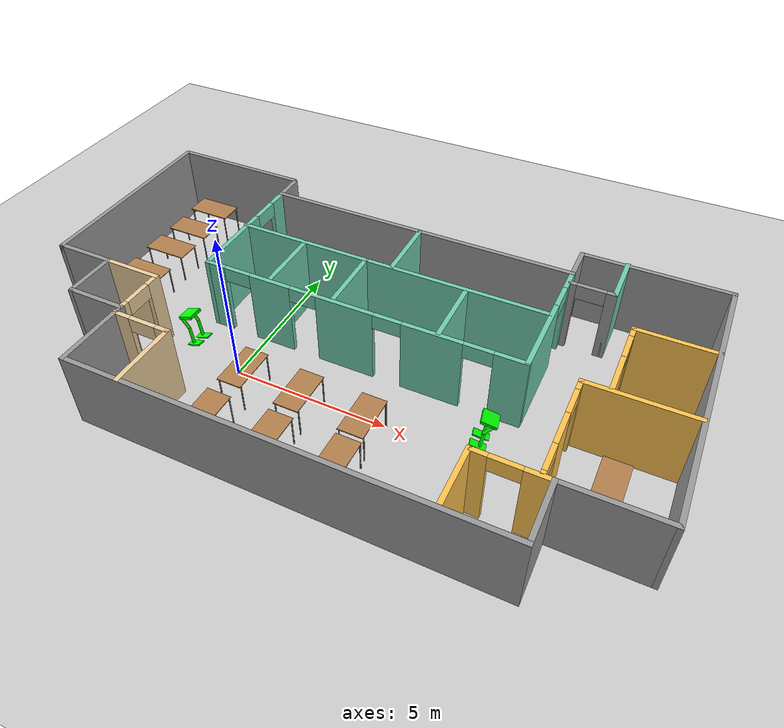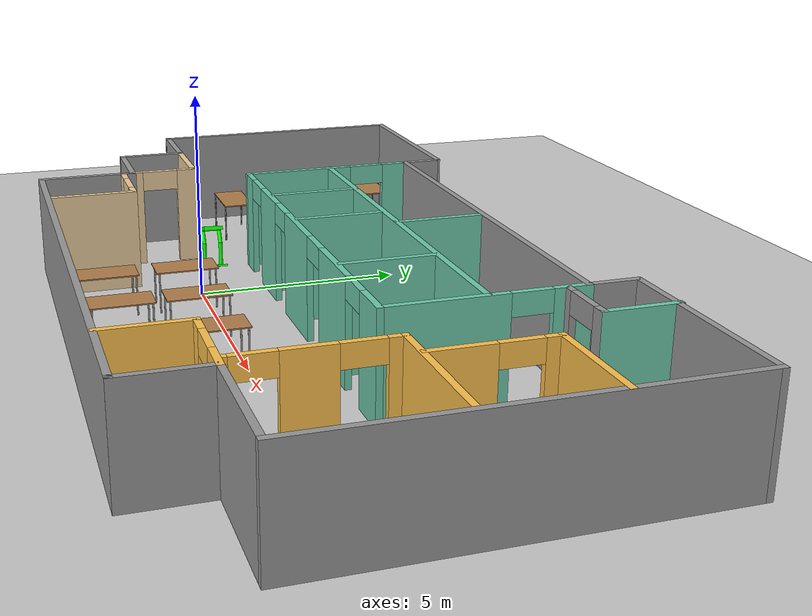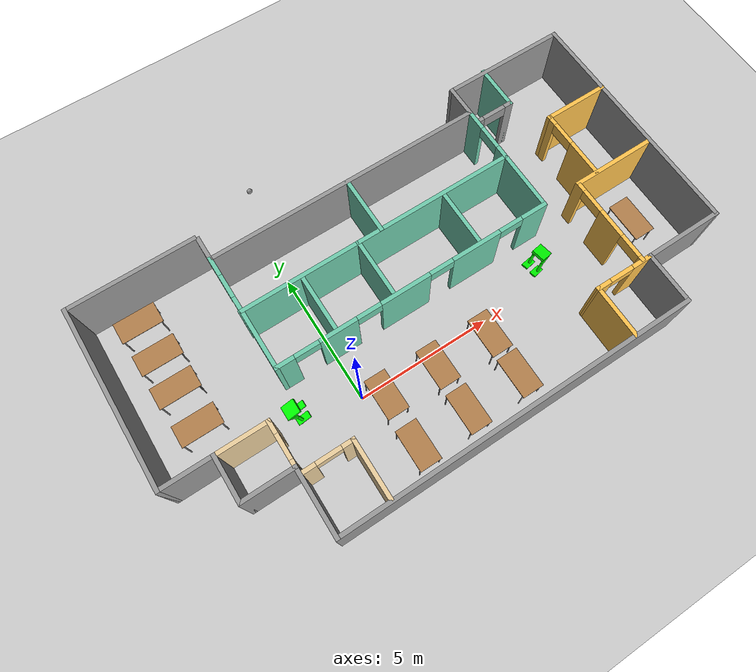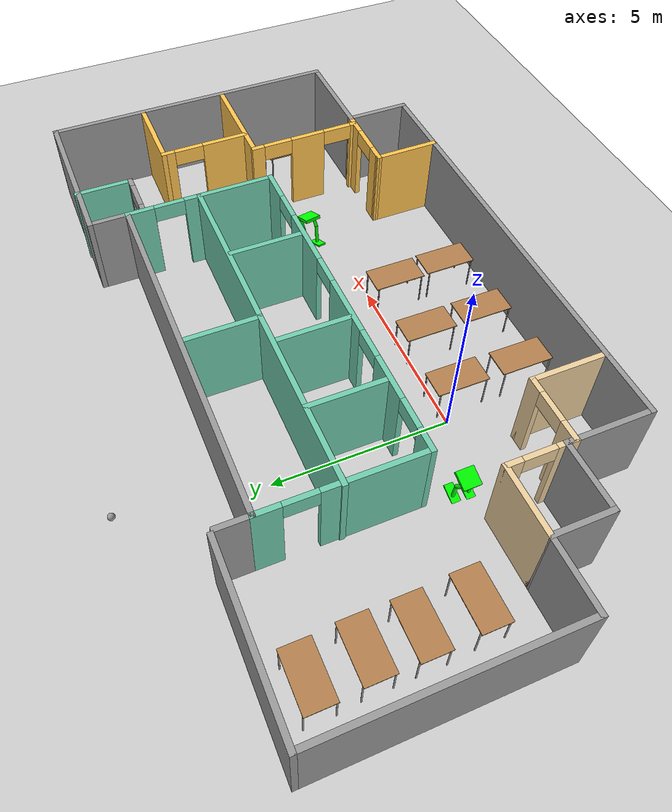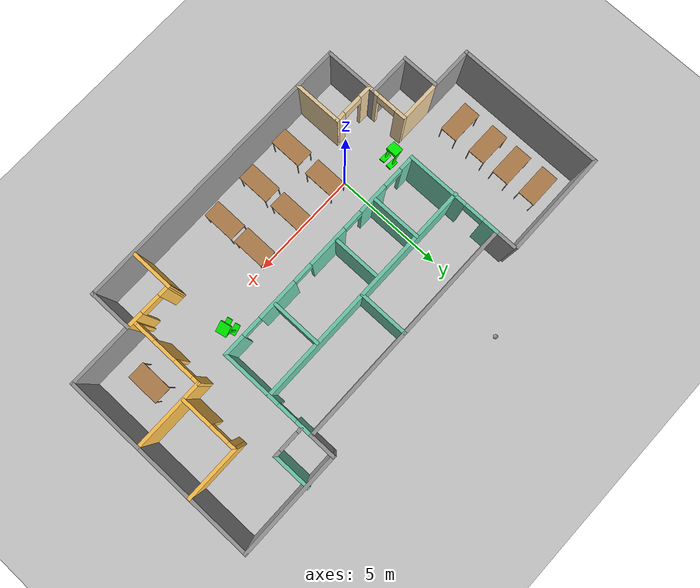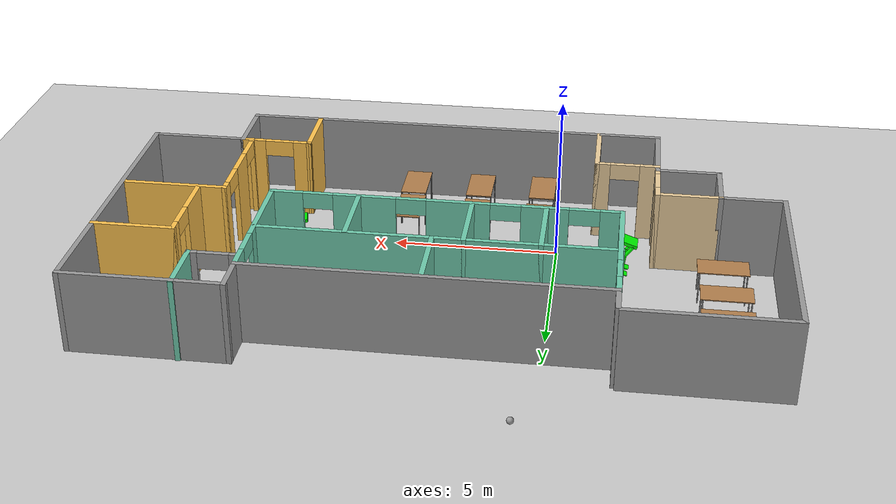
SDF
<sdf version="1.7">
 <world name="default">
  <light name="sun" type="directional">
   <pose>0 0 10 0 -0 0</pose>
   <diffuse>0.8 0.8 0.8 1</diffuse>
   <specular>0.2 0.2 0.2 1</specular>
   <attenuation>
    <range>1000</range>
    <constant>0.9</constant>
    <linear>0.01</linear>
    <quadratic>0.001</quadratic>
   </attenuation>
   <direction>-0.5 0.1 -0.9</direction>
   <spot><inner_angle>0</inner_angle><outer_angle>0</outer_angle><falloff>0</falloff></spot>
  </light>
  <model name="ground_plane">
   <static>1</static>
   <link name="link">
    <collision name="collision">
     <geometry><plane><normal>0 0 1</normal><size>100 100</size></plane></geometry>
     <surface>
      <contact><collide_bitmask>65535</collide_bitmask></contact>
      <friction><ode><mu>100</mu><mu2>50</mu2></ode></friction>
     </surface>
    </collision>
    <visual name="visual">
     <cast_shadows>0</cast_shadows>
     <geometry><plane><normal>0 0 1</normal><size>100 100</size></plane></geometry>
     <material>
      <script><uri>file://media/materials/scripts/gazebo.material</uri><name>Gazebo/Grey</name></script>
     </material>
    </visual>
   </link>
  </model>
  <gravity>0 0 -9.8</gravity>
  <magnetic_field>6e-06 2.3e-05 -4.2e-05</magnetic_field>
  <atmosphere type="adiabatic"/>
  <physics type="ode">
   <max_step_size>0.001</max_step_size>
   <real_time_factor>1</real_time_factor>
   <real_time_update_rate>1000</real_time_update_rate>
  </physics>
  <scene><ambient>0.4 0.4 0.4 1</ambient><background>0.7 0.7 0.7 1</background><shadows>1</shadows></scene>
  <spherical_coordinates>
   <surface_model>EARTH_WGS84</surface_model>
   <latitude_deg>0</latitude_deg>
   <longitude_deg>0</longitude_deg>
   <elevation>0</elevation>
   <heading_deg>0</heading_deg>
  </spherical_coordinates>
  <model name="HumanoidRobot">
   <link name="link_0">
    <inertial>
     <mass>1</mass>
     <inertia>
      <ixx>0.166667</ixx>
      <ixy>0</ixy>
      <ixz>0</ixz>
      <iyy>0.166667</iyy>
      <iyz>0</iyz>
      <izz>0.166667</izz>
     </inertia>
    </inertial>
    <pose>-0.088426 0.010705 0.536121 0 -0 0</pose>
    <visual name="visual">
     <geometry><box><size>0.5 0.5 0.1</size></box></geometry>
     <material>
      <lighting>1</lighting>
      <script><uri>file://media/materials/scripts/gazebo.material</uri><name>Gazebo/Grey</name></script>
      <shader type="pixel"><normal_map>__default__</normal_map></shader>
      <ambient>0 1 0 1</ambient>
      <diffuse>0.7 0.7 0.7 1</diffuse>
      <specular>0.01 0.01 0.01 1</specular>
      <emissive>0 0 0 1</emissive>
     </material>
    </visual>
    <collision name="collision">
     <geometry><box><size>0.5 0.5 0.1</size></box></geometry>
     <surface>
      <friction>
       <ode><mu>1</mu><mu2>1</mu2><fdir1>0 0 0</fdir1><slip1>0</slip1><slip2>0</slip2></ode>
       <torsional>
        <coefficient>1</coefficient>
        <patch_radius>0</patch_radius>
        <surface_radius>0</surface_radius>
        <use_patch_radius>1</use_patch_radius>
        <ode><slip>0</slip></ode>
       </torsional>
      </friction>
      <bounce><restitution_coefficient>0</restitution_coefficient><threshold>1e+06</threshold></bounce>
      <contact>
       <collide_without_contact>0</collide_without_contact>
       <collide_without_contact_bitmask>1</collide_without_contact_bitmask>
       <collide_bitmask>1</collide_bitmask>
       <ode>
        <soft_cfm>0</soft_cfm>
        <soft_erp>0.2</soft_erp>
        <kp>1e+13</kp>
        <kd>1</kd>
        <max_vel>0.01</max_vel>
        <min_depth>0</min_depth>
       </ode>
       <bullet>
        <split_impulse>1</split_impulse>
        <split_impulse_penetration_threshold>-0.01</split_impulse_penetration_threshold>
        <soft_cfm>0</soft_cfm>
        <soft_erp>0.2</soft_erp>
        <kp>1e+13</kp>
        <kd>1</kd>
       </bullet>
      </contact>
     </surface>
    </collision>
   </link>
   <link name="link_1">
    <inertial>
     <mass>1</mass>
     <inertia>
      <ixx>0.166667</ixx>
      <ixy>0</ixy>
      <ixz>0</ixz>
      <iyy>0.166667</iyy>
      <iyz>0</iyz>
      <izz>0.166667</izz>
     </inertia>
    </inertial>
    <pose>-0.002836 -0.189031 -0.453961 0 -0 0</pose>
    <visual name="visual">
     <geometry><box><size>0.5 0.25 0.05</size></box></geometry>
     <material>
      <lighting>1</lighting>
      <script><uri>file://media/materials/scripts/gazebo.material</uri><name>Gazebo/Grey</name></script>
      <shader type="pixel"><normal_map>__default__</normal_map></shader>
      <ambient>0 1 0 1</ambient>
      <diffuse>0.7 0.7 0.7 1</diffuse>
      <specular>0.01 0.01 0.01 1</specular>
      <emissive>0 0 0 1</emissive>
     </material>
    </visual>
    <collision name="collision">
     <geometry><box><size>0.5 0.25 0.05</size></box></geometry>
     <surface>
      <friction>
       <ode><mu>1</mu><mu2>1</mu2><fdir1>0 0 0</fdir1><slip1>0</slip1><slip2>0</slip2></ode>
       <torsional>
        <coefficient>1</coefficient>
        <patch_radius>0</patch_radius>
        <surface_radius>0</surface_radius>
        <use_patch_radius>1</use_patch_radius>
        <ode><slip>0</slip></ode>
       </torsional>
      </friction>
      <bounce><restitution_coefficient>0</restitution_coefficient><threshold>1e+06</threshold></bounce>
      <contact>
       <collide_without_contact>0</collide_without_contact>
       <collide_without_contact_bitmask>1</collide_without_contact_bitmask>
       <collide_bitmask>1</collide_bitmask>
       <ode>
        <soft_cfm>0</soft_cfm>
        <soft_erp>0.2</soft_erp>
        <kp>1e+13</kp>
        <kd>1</kd>
        <max_vel>0.01</max_vel>
        <min_depth>0</min_depth>
       </ode>
       <bullet>
        <split_impulse>1</split_impulse>
        <split_impulse_penetration_threshold>-0.01</split_impulse_penetration_threshold>
        <soft_cfm>0</soft_cfm>
        <soft_erp>0.2</soft_erp>
        <kp>1e+13</kp>
        <kd>1</kd>
       </bullet>
      </contact>
     </surface>
    </collision>
   </link>
   <link name="link_1_clone">
    <inertial>
     <mass>1</mass>
     <inertia>
      <ixx>0.166667</ixx>
      <ixy>0</ixy>
      <ixz>0</ixz>
      <iyy>0.166667</iyy>
      <iyz>0</iyz>
      <izz>0.166667</izz>
     </inertia>
    </inertial>
    <pose>0.031524 0.211991 -0.453961 0 -0 0</pose>
    <visual name="visual">
     <geometry><box><size>0.5 0.25 0.05</size></box></geometry>
     <material>
      <lighting>1</lighting>
      <script><uri>file://media/materials/scripts/gazebo.material</uri><name>Gazebo/Grey</name></script>
      <shader type="pixel"><normal_map>__default__</normal_map></shader>
      <ambient>0 1 0 1</ambient>
      <diffuse>0.7 0.7 0.7 1</diffuse>
      <specular>0.01 0.01 0.01 1</specular>
      <emissive>0 0 0 1</emissive>
     </material>
    </visual>
    <collision name="collision">
     <geometry><box><size>0.5 0.25 0.05</size></box></geometry>
     <surface>
      <friction>
       <ode><mu>1</mu><mu2>1</mu2><fdir1>0 0 0</fdir1><slip1>0</slip1><slip2>0</slip2></ode>
       <torsional>
        <coefficient>1</coefficient>
        <patch_radius>0</patch_radius>
        <surface_radius>0</surface_radius>
        <use_patch_radius>1</use_patch_radius>
        <ode><slip>0</slip></ode>
       </torsional>
      </friction>
      <bounce><restitution_coefficient>0</restitution_coefficient><threshold>1e+06</threshold></bounce>
      <contact>
       <collide_without_contact>0</collide_without_contact>
       <collide_without_contact_bitmask>1</collide_without_contact_bitmask>
       <collide_bitmask>1</collide_bitmask>
       <ode>
        <soft_cfm>0</soft_cfm>
        <soft_erp>0.2</soft_erp>
        <kp>1e+13</kp>
        <kd>1</kd>
        <max_vel>0.01</max_vel>
        <min_depth>0</min_depth>
       </ode>
       <bullet>
        <split_impulse>1</split_impulse>
        <split_impulse_penetration_threshold>-0.01</split_impulse_penetration_threshold>
        <soft_cfm>0</soft_cfm>
        <soft_erp>0.2</soft_erp>
        <kp>1e+13</kp>
        <kd>1</kd>
       </bullet>
      </contact>
     </surface>
    </collision>
   </link>
   <link name="link_2">
    <inertial>
     <mass>1</mass>
     <inertia><ixx>0.145833</ixx><ixy>0</ixy><ixz>0</ixz><iyy>0.145833</iyy><iyz>0</iyz><izz>0.125</izz></inertia>
    </inertial>
    <pose>-0.002516 -0.205584 0.325243 0 0.295116 0</pose>
    <visual name="visual">
     <geometry><cylinder><radius>0.05</radius><length>0.4</length></cylinder></geometry>
     <material>
      <lighting>1</lighting>
      <script><uri>file://media/materials/scripts/gazebo.material</uri><name>Gazebo/Grey</name></script>
      <shader type="pixel"><normal_map>__default__</normal_map></shader>
      <ambient>0 1 0 1</ambient>
      <diffuse>0.7 0.7 0.7 1</diffuse>
      <specular>0.01 0.01 0.01 1</specular>
      <emissive>0 0 0 1</emissive>
     </material>
    </visual>
    <collision name="collision">
     <geometry><cylinder><radius>0.05</radius><length>0.4</length></cylinder></geometry>
     <surface>
      <friction>
       <ode><mu>1</mu><mu2>1</mu2><fdir1>0 0 0</fdir1><slip1>0</slip1><slip2>0</slip2></ode>
       <torsional>
        <coefficient>1</coefficient>
        <patch_radius>0</patch_radius>
        <surface_radius>0</surface_radius>
        <use_patch_radius>1</use_patch_radius>
        <ode><slip>0</slip></ode>
       </torsional>
      </friction>
      <bounce><restitution_coefficient>0</restitution_coefficient><threshold>1e+06</threshold></bounce>
      <contact>
       <collide_without_contact>0</collide_without_contact>
       <collide_without_contact_bitmask>1</collide_without_contact_bitmask>
       <collide_bitmask>1</collide_bitmask>
       <ode>
        <soft_cfm>0</soft_cfm>
        <soft_erp>0.2</soft_erp>
        <kp>1e+13</kp>
        <kd>1</kd>
        <max_vel>0.01</max_vel>
        <min_depth>0</min_depth>
       </ode>
       <bullet>
        <split_impulse>1</split_impulse>
        <split_impulse_penetration_threshold>-0.01</split_impulse_penetration_threshold>
        <soft_cfm>0</soft_cfm>
        <soft_erp>0.2</soft_erp>
        <kp>1e+13</kp>
        <kd>1</kd>
       </bullet>
      </contact>
     </surface>
    </collision>
   </link>
   <link name="link_2_clone_0">
    <inertial>
     <mass>1</mass>
     <inertia><ixx>0.145833</ixx><ixy>0</ixy><ixz>0</ixz><iyy>0.145833</iyy><iyz>0</iyz><izz>0.125</izz></inertia>
    </inertial>
    <pose>0.033564 0.221349 0.325243 0 0.295116 0</pose>
    <visual name="visual">
     <geometry><cylinder><radius>0.05</radius><length>0.4</length></cylinder></geometry>
     <material>
      <lighting>1</lighting>
      <script><uri>file://media/materials/scripts/gazebo.material</uri><name>Gazebo/Grey</name></script>
      <shader type="pixel"><normal_map>__default__</normal_map></shader>
      <ambient>0 1 0 1</ambient>
      <diffuse>0.7 0.7 0.7 1</diffuse>
      <specular>0.01 0.01 0.01 1</specular>
      <emissive>0 0 0 1</emissive>
     </material>
    </visual>
    <collision name="collision">
     <geometry><cylinder><radius>0.05</radius><length>0.4</length></cylinder></geometry>
     <surface>
      <friction>
       <ode><mu>1</mu><mu2>1</mu2><fdir1>0 0 0</fdir1><slip1>0</slip1><slip2>0</slip2></ode>
       <torsional>
        <coefficient>1</coefficient>
        <patch_radius>0</patch_radius>
        <surface_radius>0</surface_radius>
        <use_patch_radius>1</use_patch_radius>
        <ode><slip>0</slip></ode>
       </torsional>
      </friction>
      <bounce><restitution_coefficient>0</restitution_coefficient><threshold>1e+06</threshold></bounce>
      <contact>
       <collide_without_contact>0</collide_without_contact>
       <collide_without_contact_bitmask>1</collide_without_contact_bitmask>
       <collide_bitmask>1</collide_bitmask>
       <ode>
        <soft_cfm>0</soft_cfm>
        <soft_erp>0.2</soft_erp>
        <kp>1e+13</kp>
        <kd>1</kd>
        <max_vel>0.01</max_vel>
        <min_depth>0</min_depth>
       </ode>
       <bullet>
        <split_impulse>1</split_impulse>
        <split_impulse_penetration_threshold>-0.01</split_impulse_penetration_threshold>
        <soft_cfm>0</soft_cfm>
        <soft_erp>0.2</soft_erp>
        <kp>1e+13</kp>
        <kd>1</kd>
       </bullet>
      </contact>
     </surface>
    </collision>
   </link>
   <link name="link_2_clone_clone">
    <inertial>
     <mass>1</mass>
     <inertia><ixx>0.145833</ixx><ixy>0</ixy><ixz>0</ixz><iyy>0.145833</iyy><iyz>0</iyz><izz>0.125</izz></inertia>
    </inertial>
    <pose>-0.002836 -0.203823 -0.139342 0 -0.190908 0</pose>
    <visual name="visual">
     <geometry><cylinder><radius>0.05</radius><length>0.6</length></cylinder></geometry>
     <material>
      <lighting>1</lighting>
      <script><uri>file://media/materials/scripts/gazebo.material</uri><name>Gazebo/Grey</name></script>
      <shader type="pixel"><normal_map>__default__</normal_map></shader>
      <ambient>0 1 0 1</ambient>
      <diffuse>0.7 0.7 0.7 1</diffuse>
      <specular>0.01 0.01 0.01 1</specular>
      <emissive>0 0 0 1</emissive>
     </material>
    </visual>
    <collision name="collision">
     <geometry><cylinder><radius>0.05</radius><length>0.6</length></cylinder></geometry>
     <surface>
      <friction>
       <ode><mu>1</mu><mu2>1</mu2><fdir1>0 0 0</fdir1><slip1>0</slip1><slip2>0</slip2></ode>
       <torsional>
        <coefficient>1</coefficient>
        <patch_radius>0</patch_radius>
        <surface_radius>0</surface_radius>
        <use_patch_radius>1</use_patch_radius>
        <ode><slip>0</slip></ode>
       </torsional>
      </friction>
      <bounce><restitution_coefficient>0</restitution_coefficient><threshold>1e+06</threshold></bounce>
      <contact>
       <collide_without_contact>0</collide_without_contact>
       <collide_without_contact_bitmask>1</collide_without_contact_bitmask>
       <collide_bitmask>1</collide_bitmask>
       <ode>
        <soft_cfm>0</soft_cfm>
        <soft_erp>0.2</soft_erp>
        <kp>1e+13</kp>
        <kd>1</kd>
        <max_vel>0.01</max_vel>
        <min_depth>0</min_depth>
       </ode>
       <bullet>
        <split_impulse>1</split_impulse>
        <split_impulse_penetration_threshold>-0.01</split_impulse_penetration_threshold>
        <soft_cfm>0</soft_cfm>
        <soft_erp>0.2</soft_erp>
        <kp>1e+13</kp>
        <kd>1</kd>
       </bullet>
      </contact>
     </surface>
    </collision>
   </link>
   <link name="link_2_clone_clone_clone">
    <inertial>
     <mass>1</mass>
     <inertia><ixx>0.145833</ixx><ixy>0</ixy><ixz>0</ixz><iyy>0.145833</iyy><iyz>0</iyz><izz>0.125</izz></inertia>
    </inertial>
    <pose>0.031524 0.2206 -0.139342 0 -0.190908 0</pose>
    <visual name="visual">
     <geometry><cylinder><radius>0.05</radius><length>0.6</length></cylinder></geometry>
     <material>
      <lighting>1</lighting>
      <script><uri>file://media/materials/scripts/gazebo.material</uri><name>Gazebo/Grey</name></script>
      <shader type="pixel"><normal_map>__default__</normal_map></shader>
      <ambient>0 1 0 1</ambient>
      <diffuse>0.7 0.7 0.7 1</diffuse>
      <specular>0.01 0.01 0.01 1</specular>
      <emissive>0 0 0 1</emissive>
     </material>
    </visual>
    <collision name="collision">
     <geometry><cylinder><radius>0.05</radius><length>0.6</length></cylinder></geometry>
     <surface>
      <friction>
       <ode><mu>1</mu><mu2>1</mu2><fdir1>0 0 0</fdir1><slip1>0</slip1><slip2>0</slip2></ode>
       <torsional>
        <coefficient>1</coefficient>
        <patch_radius>0</patch_radius>
        <surface_radius>0</surface_radius>
        <use_patch_radius>1</use_patch_radius>
        <ode><slip>0</slip></ode>
       </torsional>
      </friction>
      <bounce><restitution_coefficient>0</restitution_coefficient><threshold>1e+06</threshold></bounce>
      <contact>
       <collide_without_contact>0</collide_without_contact>
       <collide_without_contact_bitmask>1</collide_without_contact_bitmask>
       <collide_bitmask>1</collide_bitmask>
       <ode>
        <soft_cfm>0</soft_cfm>
        <soft_erp>0.2</soft_erp>
        <kp>1e+13</kp>
        <kd>1</kd>
        <max_vel>0.01</max_vel>
        <min_depth>0</min_depth>
       </ode>
       <bullet>
        <split_impulse>1</split_impulse>
        <split_impulse_penetration_threshold>-0.01</split_impulse_penetration_threshold>
        <soft_cfm>0</soft_cfm>
        <soft_erp>0.2</soft_erp>
        <kp>1e+13</kp>
        <kd>1</kd>
       </bullet>
      </contact>
     </surface>
    </collision>
   </link>
   <joint name="link_0_JOINT_0" type="revolute">
    <parent>link_0</parent>
    <child>link_2</child>
    <axis>
     <xyz>0 0 1</xyz>
     <limit>
      <lower>-1.79769e+308</lower>
      <upper>1.79769e+308</upper>
      <effort>-1</effort>
      <velocity>-1</velocity>
     </limit>
     <dynamics>
      <spring_reference>0</spring_reference>
      <spring_stiffness>0</spring_stiffness>
      <damping>0</damping>
      <friction>0</friction>
     </dynamics>
    </axis>
    <physics>
     <ode><limit><cfm>0</cfm><erp>0.2</erp></limit><suspension><cfm>0</cfm><erp>0.2</erp></suspension></ode>
    </physics>
   </joint>
   <joint name="link_0_JOINT_1" type="revolute">
    <parent>link_0</parent>
    <child>link_2_clone_0</child>
    <axis>
     <xyz>0 0 1</xyz>
     <limit>
      <lower>-1.79769e+308</lower>
      <upper>1.79769e+308</upper>
      <effort>-1</effort>
      <velocity>-1</velocity>
     </limit>
     <dynamics>
      <spring_reference>0</spring_reference>
      <spring_stiffness>0</spring_stiffness>
      <damping>0</damping>
      <friction>0</friction>
     </dynamics>
    </axis>
    <physics>
     <ode><limit><cfm>0</cfm><erp>0.2</erp></limit><suspension><cfm>0</cfm><erp>0.2</erp></suspension></ode>
    </physics>
   </joint>
   <joint name="link_2_JOINT_3" type="revolute">
    <parent>link_2</parent>
    <child>link_2_clone_clone</child>
    <axis>
     <xyz>0 0 1</xyz>
     <limit>
      <lower>-1.79769e+308</lower>
      <upper>1.79769e+308</upper>
      <effort>-1</effort>
      <velocity>-1</velocity>
     </limit>
     <dynamics>
      <spring_reference>0</spring_reference>
      <spring_stiffness>0</spring_stiffness>
      <damping>0</damping>
      <friction>0</friction>
     </dynamics>
    </axis>
    <physics>
     <ode><limit><cfm>0</cfm><erp>0.2</erp></limit><suspension><cfm>0</cfm><erp>0.2</erp></suspension></ode>
    </physics>
   </joint>
   <joint name="link_2_clone_0_JOINT_4" type="revolute">
    <parent>link_2_clone_0</parent>
    <child>link_2_clone_clone_clone</child>
    <axis>
     <xyz>0 0 1</xyz>
     <limit>
      <lower>-1.79769e+308</lower>
      <upper>1.79769e+308</upper>
      <effort>-1</effort>
      <velocity>-1</velocity>
     </limit>
     <dynamics>
      <spring_reference>0</spring_reference>
      <spring_stiffness>0</spring_stiffness>
      <damping>0</damping>
      <friction>0</friction>
     </dynamics>
    </axis>
    <physics>
     <ode><limit><cfm>0</cfm><erp>0.2</erp></limit><suspension><cfm>0</cfm><erp>0.2</erp></suspension></ode>
    </physics>
   </joint>
   <joint name="link_2_clone_clone_JOINT_5" type="revolute">
    <parent>link_2_clone_clone</parent>
    <child>link_1</child>
    <axis>
     <xyz>0 0 1</xyz>
     <limit>
      <lower>-1.79769e+308</lower>
      <upper>1.79769e+308</upper>
      <effort>-1</effort>
      <velocity>-1</velocity>
     </limit>
     <dynamics>
      <spring_reference>0</spring_reference>
      <spring_stiffness>0</spring_stiffness>
      <damping>0</damping>
      <friction>0</friction>
     </dynamics>
    </axis>
    <physics>
     <ode><limit><cfm>0</cfm><erp>0.2</erp></limit><suspension><cfm>0</cfm><erp>0.2</erp></suspension></ode>
    </physics>
   </joint>
   <joint name="link_2_clone_clone_clone_JOINT_6" type="revolute">
    <parent>link_2_clone_clone_clone</parent>
    <child>link_1_clone</child>
    <axis>
     <xyz>0 0 1</xyz>
     <limit>
      <lower>-1.79769e+308</lower>
      <upper>1.79769e+308</upper>
      <effort>-1</effort>
      <velocity>-1</velocity>
     </limit>
     <dynamics>
      <spring_reference>0</spring_reference>
      <spring_stiffness>0</spring_stiffness>
      <damping>0</damping>
      <friction>0</friction>
     </dynamics>
    </axis>
    <physics>
     <ode><limit><cfm>0</cfm><erp>0.2</erp></limit><suspension><cfm>0</cfm><erp>0.2</erp></suspension></ode>
    </physics>
   </joint>
   <static>0</static>
   <pose>-2.1027 0.733503 0.473362 0.028454 0.335167 -3.13391</pose>
  </model>
  <model name="Building">
   <pose>3.19653 1.84983 0 0 -0 0</pose>
   <link name="Wall_0">
    <collision name="Wall_0_Collision">
     <geometry><box><size>4.75 0.15 2.5</size></box></geometry>
     <pose>0 0 1.25 0 -0 0</pose>
    </collision>
    <visual name="Wall_0_Visual">
     <pose>0 0 1.25 0 -0 0</pose>
     <geometry><box><size>4.75 0.15 2.5</size></box></geometry>
     <material>
      <script><uri>file://media/materials/scripts/gazebo.material</uri><name>Gazebo/Grey</name></script>
      <ambient>1 1 1 1</ambient>
     </material>
     <meta><layer>0</layer></meta>
    </visual>
    <pose>-7.525 5.17858 0 0 -0 3.14159</pose>
   </link>
   <link name="Wall_1">
    <collision name="Wall_1_Collision">
     <geometry><box><size>6.75 0.15 2.5</size></box></geometry>
     <pose>0 0 1.25 0 -0 0</pose>
    </collision>
    <visual name="Wall_1_Visual">
     <pose>0 0 1.25 0 -0 0</pose>
     <geometry><box><size>6.75 0.15 2.5</size></box></geometry>
     <material>
      <script><uri>file://media/materials/scripts/gazebo.material</uri><name>Gazebo/Grey</name></script>
      <ambient>1 1 1 1</ambient>
     </material>
     <meta><layer>0</layer></meta>
    </visual>
    <pose>-9.825 1.87858 0 0 -0 -1.5708</pose>
   </link>
   <link name="Wall_10">
    <collision name="Wall_10_Collision">
     <geometry><box><size>4.75 0.15 2.5</size></box></geometry>
     <pose>0 0 1.25 0 -0 0</pose>
    </collision>
    <visual name="Wall_10_Visual">
     <pose>0 0 1.25 0 -0 0</pose>
     <geometry><box><size>4.75 0.15 2.5</size></box></geometry>
     <material>
      <script><uri>file://media/materials/scripts/gazebo.material</uri><name>Gazebo/Grey</name></script>
      <ambient>1 1 1 1</ambient>
     </material>
     <meta><layer>0</layer></meta>
    </visual>
    <pose>7.525 5.32857 0 0 -0 3.14159</pose>
   </link>
   <link name="Wall_11">
    <collision name="Wall_11_Collision">
     <geometry><box><size>1.25 0.15 2.5</size></box></geometry>
     <pose>0 0 1.25 0 -0 0</pose>
    </collision>
    <visual name="Wall_11_Visual">
     <pose>0 0 1.25 0 -0 0</pose>
     <geometry><box><size>1.25 0.15 2.5</size></box></geometry>
     <material>
      <script><uri>file://media/materials/scripts/gazebo.material</uri><name>Gazebo/Grey</name></script>
      <ambient>1 1 1 1</ambient>
     </material>
     <meta><layer>0</layer></meta>
    </visual>
    <pose>5.225 4.77858 0 0 -0 -1.5708</pose>
   </link>
   <link name="Wall_15">
    <collision name="Wall_15_Collision">
     <geometry><box><size>10.5 0.15 2.5</size></box></geometry>
     <pose>0 0 1.25 0 -0 0</pose>
    </collision>
    <visual name="Wall_15_Visual">
     <pose>0 0 1.25 0 -0 0</pose>
     <geometry><box><size>10.5 0.15 2.5</size></box></geometry>
     <material>
      <script><uri>file://media/materials/scripts/gazebo.material</uri><name>Gazebo/Grey</name></script>
      <ambient>1 1 1 1</ambient>
     </material>
     <meta><layer>0</layer></meta>
    </visual>
    <pose>0.05 4.22858 0 0 -0 3.14159</pose>
   </link>
   <link name="Wall_18">
    <collision name="Wall_18_Collision">
     <geometry><box><size>2 0.15 2.5</size></box></geometry>
     <pose>0 0 1.25 0 -0 0</pose>
    </collision>
    <visual name="Wall_18_Visual">
     <pose>0 0 1.25 0 -0 0</pose>
     <geometry><box><size>2 0.15 2.5</size></box></geometry>
     <material>
      <script><uri>file://media/materials/scripts/gazebo.material</uri><name>Gazebo/Grey</name></script>
      <ambient>0.921569 0.807843 0.615686 1</ambient>
     </material>
     <meta><layer>0</layer></meta>
    </visual>
    <pose>-7.05 -1.42142 0 0 -0 0</pose>
   </link>
   <link name="Wall_19">
    <pose>-6.125 -2.34642 0 0 -0 -1.5708</pose>
    <visual name="Wall_19_Visual_0">
     <pose>-0.740197 0 1.25 0 -0 0</pose>
     <geometry><box><size>0.519606 0.15 2.5</size></box></geometry>
     <material>
      <script><uri>file://media/materials/scripts/gazebo.material</uri><name>Gazebo/Grey</name></script>
      <ambient>0.921569 0.807843 0.615686 1</ambient>
     </material>
     <meta><layer>0</layer></meta>
    </visual>
    <collision name="Wall_19_Collision_0">
     <geometry><box><size>0.519606 0.15 2.5</size></box></geometry>
     <pose>-0.740197 0 1.25 0 -0 0</pose>
    </collision>
    <visual name="Wall_19_Visual_1">
     <pose>0.709803 0 1.25 0 -0 0</pose>
     <geometry><box><size>0.580394 0.15 2.5</size></box></geometry>
     <material>
      <script><uri>file://media/materials/scripts/gazebo.material</uri><name>Gazebo/Grey</name></script>
      <ambient>0.921569 0.807843 0.615686 1</ambient>
     </material>
     <meta><layer>0</layer></meta>
    </visual>
    <collision name="Wall_19_Collision_1">
     <geometry><box><size>0.580394 0.15 2.5</size></box></geometry>
     <pose>0.709803 0 1.25 0 -0 0</pose>
    </collision>
    <visual name="Wall_19_Visual_2">
     <pose>-0.030394 0 2.25 0 -0 0</pose>
     <geometry><box><size>0.9 0.15 0.5</size></box></geometry>
     <material>
      <script><uri>file://media/materials/scripts/gazebo.material</uri><name>Gazebo/Grey</name></script>
      <ambient>0.921569 0.807843 0.615686 1</ambient>
     </material>
     <meta><layer>0</layer></meta>
    </visual>
    <collision name="Wall_19_Collision_2">
     <geometry><box><size>0.9 0.15 0.5</size></box></geometry>
     <pose>-0.030394 0 2.25 0 -0 0</pose>
    </collision>
   </link>
   <link name="Wall_2">
    <collision name="Wall_2_Collision">
     <geometry><box><size>2 0.15 2.5</size></box></geometry>
     <pose>0 0 1.25 0 -0 0</pose>
    </collision>
    <visual name="Wall_2_Visual">
     <pose>0 0 1.25 0 -0 0</pose>
     <geometry><box><size>2 0.15 2.5</size></box></geometry>
     <material>
      <script><uri>file://media/materials/scripts/gazebo.material</uri><name>Gazebo/Grey</name></script>
      <ambient>1 1 1 1</ambient>
     </material>
     <meta><layer>0</layer></meta>
    </visual>
    <pose>-8.9 -1.42142 0 0 -0 0</pose>
   </link>
   <link name="Wall_20">
    <pose>-5.2 -3.27142 0 0 -0 0</pose>
    <visual name="Wall_20_Visual_0">
     <pose>-0.691615 0 1.25 0 -0 0</pose>
     <geometry><box><size>0.616771 0.15 2.5</size></box></geometry>
     <material>
      <script><uri>file://media/materials/scripts/gazebo.material</uri><name>Gazebo/Grey</name></script>
      <ambient>0.921569 0.807843 0.615686 1</ambient>
     </material>
     <meta><layer>0</layer></meta>
    </visual>
    <collision name="Wall_20_Collision_0">
     <geometry><box><size>0.616771 0.15 2.5</size></box></geometry>
     <pose>-0.691615 0 1.25 0 -0 0</pose>
    </collision>
    <visual name="Wall_20_Visual_1">
     <pose>0.758385 0 1.25 0 -0 0</pose>
     <geometry><box><size>0.483229 0.15 2.5</size></box></geometry>
     <material>
      <script><uri>file://media/materials/scripts/gazebo.material</uri><name>Gazebo/Grey</name></script>
      <ambient>0.921569 0.807843 0.615686 1</ambient>
     </material>
     <meta><layer>0</layer></meta>
    </visual>
    <collision name="Wall_20_Collision_1">
     <geometry><box><size>0.483229 0.15 2.5</size></box></geometry>
     <pose>0.758385 0 1.25 0 -0 0</pose>
    </collision>
    <visual name="Wall_20_Visual_2">
     <pose>0.066771 0 2.25 0 -0 0</pose>
     <geometry><box><size>0.9 0.15 0.5</size></box></geometry>
     <material>
      <script><uri>file://media/materials/scripts/gazebo.material</uri><name>Gazebo/Grey</name></script>
      <ambient>0.921569 0.807843 0.615686 1</ambient>
     </material>
     <meta><layer>0</layer></meta>
    </visual>
    <collision name="Wall_20_Collision_2">
     <geometry><box><size>0.9 0.15 0.5</size></box></geometry>
     <pose>0.066771 0 2.25 0 -0 0</pose>
    </collision>
   </link>
   <link name="Wall_21">
    <collision name="Wall_21_Collision">
     <geometry><box><size>2.25 0.15 2.5</size></box></geometry>
     <pose>0 0 1.25 0 -0 0</pose>
    </collision>
    <visual name="Wall_21_Visual">
     <pose>0 0 1.25 0 -0 0</pose>
     <geometry><box><size>2.25 0.15 2.5</size></box></geometry>
     <material>
      <script><uri>file://media/materials/scripts/gazebo.material</uri><name>Gazebo/Grey</name></script>
      <ambient>0.921569 0.807843 0.615686 1</ambient>
     </material>
     <meta><layer>0</layer></meta>
    </visual>
    <pose>-4.275 -4.32142 0 0 -0 -1.5708</pose>
   </link>
   <link name="Wall_23">
    <collision name="Wall_23_Collision">
     <geometry><box><size>2 0.15 2.5</size></box></geometry>
     <pose>0 0 1.25 0 -0 0</pose>
    </collision>
    <visual name="Wall_23_Visual">
     <pose>0 0 1.25 0 -0 0</pose>
     <geometry><box><size>2 0.15 2.5</size></box></geometry>
     <material>
      <script><uri>file://media/materials/scripts/gazebo.material</uri><name>Gazebo/Grey</name></script>
      <ambient>1 0.764706 0.305882 1</ambient>
     </material>
     <meta><layer>0</layer></meta>
    </visual>
    <pose>4.83918 -4.41946 0 0 -0 1.5708</pose>
   </link>
   <link name="Wall_24">
    <pose>5.90709 -3.50794 0 0 -0 -0.012623</pose>
    <visual name="Wall_24_Visual_0">
     <pose>-0.856676 0 1.25 0 -0 0</pose>
     <geometry><box><size>0.572633 0.15 2.5</size></box></geometry>
     <material>
      <script><uri>file://media/materials/scripts/gazebo.material</uri><name>Gazebo/Grey</name></script>
      <ambient>1 0.764706 0.305882 1</ambient>
     </material>
     <meta><layer>0</layer></meta>
    </visual>
    <collision name="Wall_24_Collision_0">
     <geometry><box><size>0.572633 0.15 2.5</size></box></geometry>
     <pose>-0.856676 0 1.25 0 -0 0</pose>
    </collision>
    <visual name="Wall_24_Visual_1">
     <pose>0.736317 0 1.25 0 -0 0</pose>
     <geometry><box><size>0.813352 0.15 2.5</size></box></geometry>
     <material>
      <script><uri>file://media/materials/scripts/gazebo.material</uri><name>Gazebo/Grey</name></script>
      <ambient>1 0.764706 0.305882 1</ambient>
     </material>
     <meta><layer>0</layer></meta>
    </visual>
    <collision name="Wall_24_Collision_1">
     <geometry><box><size>0.813352 0.15 2.5</size></box></geometry>
     <pose>0.736317 0 1.25 0 -0 0</pose>
    </collision>
    <visual name="Wall_24_Visual_2">
     <pose>-0.120359 0 2.25 0 -0 0</pose>
     <geometry><box><size>0.9 0.15 0.5</size></box></geometry>
     <material>
      <script><uri>file://media/materials/scripts/gazebo.material</uri><name>Gazebo/Grey</name></script>
      <ambient>1 0.764706 0.305882 1</ambient>
     </material>
     <meta><layer>0</layer></meta>
    </visual>
    <collision name="Wall_24_Collision_2">
     <geometry><box><size>0.9 0.15 0.5</size></box></geometry>
     <pose>-0.120359 0 2.25 0 -0 0</pose>
    </collision>
   </link>
   <link name="Wall_26">
    <pose>6.6746 -1.80346 0 0 -0 1.5708</pose>
    <visual name="Wall_26_Visual_0">
     <pose>-1.64689 0 1.25 0 -0 0</pose>
     <geometry><box><size>0.206214 0.15 2.5</size></box></geometry>
     <material>
      <script><uri>file://media/materials/scripts/gazebo.material</uri><name>Gazebo/Grey</name></script>
      <ambient>1 0.764706 0.305882 1</ambient>
     </material>
     <meta><layer>0</layer></meta>
    </visual>
    <collision name="Wall_26_Collision_0">
     <geometry><box><size>0.206214 0.15 2.5</size></box></geometry>
     <pose>-1.64689 0 1.25 0 -0 0</pose>
    </collision>
    <visual name="Wall_26_Visual_1">
     <pose>-0.099603 0 1.25 0 -0 0</pose>
     <geometry><box><size>1.08837 0.15 2.5</size></box></geometry>
     <material>
      <script><uri>file://media/materials/scripts/gazebo.material</uri><name>Gazebo/Grey</name></script>
      <ambient>1 0.764706 0.305882 1</ambient>
     </material>
     <meta><layer>0</layer></meta>
    </visual>
    <collision name="Wall_26_Collision_1">
     <geometry><box><size>1.08837 0.15 2.5</size></box></geometry>
     <pose>-0.099603 0 1.25 0 -0 0</pose>
    </collision>
    <visual name="Wall_26_Visual_2">
     <pose>1.54729 0 1.25 0 -0 0</pose>
     <geometry><box><size>0.405421 0.15 2.5</size></box></geometry>
     <material>
      <script><uri>file://media/materials/scripts/gazebo.material</uri><name>Gazebo/Grey</name></script>
      <ambient>1 0.764706 0.305882 1</ambient>
     </material>
     <meta><layer>0</layer></meta>
    </visual>
    <collision name="Wall_26_Collision_2">
     <geometry><box><size>0.405421 0.15 2.5</size></box></geometry>
     <pose>1.54729 0 1.25 0 -0 0</pose>
    </collision>
    <visual name="Wall_26_Visual_3">
     <pose>-1.09379 0 2.25 0 -0 0</pose>
     <geometry><box><size>0.9 0.15 0.5</size></box></geometry>
     <material>
      <script><uri>file://media/materials/scripts/gazebo.material</uri><name>Gazebo/Grey</name></script>
      <ambient>1 0.764706 0.305882 1</ambient>
     </material>
     <meta><layer>0</layer></meta>
    </visual>
    <collision name="Wall_26_Collision_3">
     <geometry><box><size>0.9 0.15 0.5</size></box></geometry>
     <pose>-1.09379 0 2.25 0 -0 0</pose>
    </collision>
    <visual name="Wall_26_Visual_4">
     <pose>0.894579 0 2.25 0 -0 0</pose>
     <geometry><box><size>0.9 0.15 0.5</size></box></geometry>
     <material>
      <script><uri>file://media/materials/scripts/gazebo.material</uri><name>Gazebo/Grey</name></script>
      <ambient>1 0.764706 0.305882 1</ambient>
     </material>
     <meta><layer>0</layer></meta>
    </visual>
    <collision name="Wall_26_Collision_4">
     <geometry><box><size>0.9 0.15 0.5</size></box></geometry>
     <pose>0.894579 0 2.25 0 -0 0</pose>
    </collision>
   </link>
   <link name="Wall_27">
    <collision name="Wall_27_Collision">
     <geometry><box><size>3.25 0.15 2.5</size></box></geometry>
     <pose>0 0 1.25 0 -0 0</pose>
    </collision>
    <visual name="Wall_27_Visual">
     <pose>0 0 1.25 0 -0 0</pose>
     <geometry><box><size>3.25 0.15 2.5</size></box></geometry>
     <material>
      <script><uri>file://media/materials/scripts/gazebo.material</uri><name>Gazebo/Grey</name></script>
      <ambient>1 0.764706 0.305882 1</ambient>
     </material>
     <meta><layer>0</layer></meta>
    </visual>
    <pose>8.2246 -0.12846 0 0 -0 0</pose>
   </link>
   <link name="Wall_29">
    <pose>7.46995 1.21706 0 0 -0 1.5708</pose>
    <visual name="Wall_29_Visual_0">
     <pose>-0.660088 0 1.25 0 -0 0</pose>
     <geometry><box><size>1.42982 0.15 2.5</size></box></geometry>
     <material>
      <script><uri>file://media/materials/scripts/gazebo.material</uri><name>Gazebo/Grey</name></script>
      <ambient>1 0.764706 0.305882 1</ambient>
     </material>
     <meta><layer>0</layer></meta>
    </visual>
    <collision name="Wall_29_Collision_0">
     <geometry><box><size>1.42982 0.15 2.5</size></box></geometry>
     <pose>-0.660088 0 1.25 0 -0 0</pose>
    </collision>
    <visual name="Wall_29_Visual_1">
     <pose>1.16491 0 1.25 0 -0 0</pose>
     <geometry><box><size>0.420177 0.15 2.5</size></box></geometry>
     <material>
      <script><uri>file://media/materials/scripts/gazebo.material</uri><name>Gazebo/Grey</name></script>
      <ambient>1 0.764706 0.305882 1</ambient>
     </material>
     <meta><layer>0</layer></meta>
    </visual>
    <collision name="Wall_29_Collision_1">
     <geometry><box><size>0.420177 0.15 2.5</size></box></geometry>
     <pose>1.16491 0 1.25 0 -0 0</pose>
    </collision>
    <visual name="Wall_29_Visual_2">
     <pose>0.504823 0 2.25 0 -0 0</pose>
     <geometry><box><size>0.9 0.15 0.5</size></box></geometry>
     <material>
      <script><uri>file://media/materials/scripts/gazebo.material</uri><name>Gazebo/Grey</name></script>
      <ambient>1 0.764706 0.305882 1</ambient>
     </material>
     <meta><layer>0</layer></meta>
    </visual>
    <collision name="Wall_29_Collision_2">
     <geometry><box><size>0.9 0.15 0.5</size></box></geometry>
     <pose>0.504823 0 2.25 0 -0 0</pose>
    </collision>
   </link>
   <link name="Wall_3">
    <collision name="Wall_3_Collision">
     <geometry><box><size>1.75 0.15 2.5</size></box></geometry>
     <pose>0 0 1.25 0 -0 0</pose>
    </collision>
    <visual name="Wall_3_Visual">
     <pose>0 0 1.25 0 -0 0</pose>
     <geometry><box><size>1.75 0.15 2.5</size></box></geometry>
     <material>
      <script><uri>file://media/materials/scripts/gazebo.material</uri><name>Gazebo/Grey</name></script>
      <ambient>1 1 1 1</ambient>
     </material>
     <meta><layer>0</layer></meta>
    </visual>
    <pose>-7.975 -2.22142 0 0 -0 -1.5708</pose>
   </link>
   <link name="Wall_30">
    <collision name="Wall_30_Collision">
     <geometry><box><size>2.5 0.15 2.5</size></box></geometry>
     <pose>0 0 1.25 0 -0 0</pose>
    </collision>
    <visual name="Wall_30_Visual">
     <pose>0 0 1.25 0 -0 0</pose>
     <geometry><box><size>2.5 0.15 2.5</size></box></geometry>
     <material>
      <script><uri>file://media/materials/scripts/gazebo.material</uri><name>Gazebo/Grey</name></script>
      <ambient>1 0.764706 0.305882 1</ambient>
     </material>
     <meta><layer>0</layer></meta>
    </visual>
    <pose>8.64494 2.51706 0 0 -0 0</pose>
   </link>
   <link name="Wall_32">
    <pose>5.225 2.05357 0 0 -0 -1.5708</pose>
    <visual name="Wall_32_Visual_0">
     <pose>-1.82655 0 1.25 0 -0 0</pose>
     <geometry><box><size>0.846906 0.15 2.5</size></box></geometry>
     <material>
      <script><uri>file://media/materials/scripts/gazebo.material</uri><name>Gazebo/Grey</name></script>
      <ambient>0.435294 0.796078 0.67451 1</ambient>
     </material>
     <meta><layer>0</layer></meta>
    </visual>
    <collision name="Wall_32_Collision_0">
     <geometry><box><size>0.846906 0.15 2.5</size></box></geometry>
     <pose>-1.82655 0 1.25 0 -0 0</pose>
    </collision>
    <visual name="Wall_32_Visual_1">
     <pose>0.873453 0 1.25 0 -0 0</pose>
     <geometry><box><size>2.75309 0.15 2.5</size></box></geometry>
     <material>
      <script><uri>file://media/materials/scripts/gazebo.material</uri><name>Gazebo/Grey</name></script>
      <ambient>0.435294 0.796078 0.67451 1</ambient>
     </material>
     <meta><layer>0</layer></meta>
    </visual>
    <collision name="Wall_32_Collision_1">
     <geometry><box><size>2.75309 0.15 2.5</size></box></geometry>
     <pose>0.873453 0 1.25 0 -0 0</pose>
    </collision>
    <visual name="Wall_32_Visual_2">
     <pose>-0.953094 0 2.25 0 -0 0</pose>
     <geometry><box><size>0.9 0.15 0.5</size></box></geometry>
     <material>
      <script><uri>file://media/materials/scripts/gazebo.material</uri><name>Gazebo/Grey</name></script>
      <ambient>0.435294 0.796078 0.67451 1</ambient>
     </material>
     <meta><layer>0</layer></meta>
    </visual>
    <collision name="Wall_32_Collision_2">
     <geometry><box><size>0.9 0.15 0.5</size></box></geometry>
     <pose>-0.953094 0 2.25 0 -0 0</pose>
    </collision>
   </link>
   <link name="Wall_33">
    <pose>0.05 -0.121425 0 0 -0 3.14159</pose>
    <visual name="Wall_33_Visual_0">
     <pose>-4.73985 0 1.25 0 -0 0</pose>
     <geometry><box><size>1.02029 0.15 2.5</size></box></geometry>
     <material>
      <script><uri>file://media/materials/scripts/gazebo.material</uri><name>Gazebo/Grey</name></script>
      <ambient>0.435294 0.796078 0.67451 1</ambient>
     </material>
     <meta><layer>0</layer></meta>
    </visual>
    <collision name="Wall_33_Collision_0">
     <geometry><box><size>1.02029 0.15 2.5</size></box></geometry>
     <pose>-4.73985 0 1.25 0 -0 0</pose>
    </collision>
    <visual name="Wall_33_Visual_1">
     <pose>-2.38785 0 1.25 0 -0 0</pose>
     <geometry><box><size>1.88371 0.15 2.5</size></box></geometry>
     <material>
      <script><uri>file://media/materials/scripts/gazebo.material</uri><name>Gazebo/Grey</name></script>
      <ambient>0.435294 0.796078 0.67451 1</ambient>
     </material>
     <meta><layer>0</layer></meta>
    </visual>
    <collision name="Wall_33_Collision_1">
     <geometry><box><size>1.88371 0.15 2.5</size></box></geometry>
     <pose>-2.38785 0 1.25 0 -0 0</pose>
    </collision>
    <visual name="Wall_33_Visual_2">
     <pose>0.395859 0 1.25 0 -0 0</pose>
     <geometry><box><size>1.88371 0.15 2.5</size></box></geometry>
     <material>
      <script><uri>file://media/materials/scripts/gazebo.material</uri><name>Gazebo/Grey</name></script>
      <ambient>0.435294 0.796078 0.67451 1</ambient>
     </material>
     <meta><layer>0</layer></meta>
    </visual>
    <collision name="Wall_33_Collision_2">
     <geometry><box><size>1.88371 0.15 2.5</size></box></geometry>
     <pose>0.395859 0 1.25 0 -0 0</pose>
    </collision>
    <visual name="Wall_33_Visual_3">
     <pose>2.93485 0 1.25 0 -0 0</pose>
     <geometry><box><size>1.39427 0.15 2.5</size></box></geometry>
     <material>
      <script><uri>file://media/materials/scripts/gazebo.material</uri><name>Gazebo/Grey</name></script>
      <ambient>0.435294 0.796078 0.67451 1</ambient>
     </material>
     <meta><layer>0</layer></meta>
    </visual>
    <collision name="Wall_33_Collision_3">
     <geometry><box><size>1.39427 0.15 2.5</size></box></geometry>
     <pose>2.93485 0 1.25 0 -0 0</pose>
    </collision>
    <visual name="Wall_33_Visual_4">
     <pose>4.89099 0 1.25 0 -0 0</pose>
     <geometry><box><size>0.718019 0.15 2.5</size></box></geometry>
     <material>
      <script><uri>file://media/materials/scripts/gazebo.material</uri><name>Gazebo/Grey</name></script>
      <ambient>0.435294 0.796078 0.67451 1</ambient>
     </material>
     <meta><layer>0</layer></meta>
    </visual>
    <collision name="Wall_33_Collision_4">
     <geometry><box><size>0.718019 0.15 2.5</size></box></geometry>
     <pose>4.89099 0 1.25 0 -0 0</pose>
    </collision>
    <visual name="Wall_33_Visual_5">
     <pose>-3.77971 0 2.25 0 -0 0</pose>
     <geometry><box><size>0.9 0.15 0.5</size></box></geometry>
     <material>
      <script><uri>file://media/materials/scripts/gazebo.material</uri><name>Gazebo/Grey</name></script>
      <ambient>0.435294 0.796078 0.67451 1</ambient>
     </material>
     <meta><layer>0</layer></meta>
    </visual>
    <collision name="Wall_33_Collision_5">
     <geometry><box><size>0.9 0.15 0.5</size></box></geometry>
     <pose>-3.77971 0 2.25 0 -0 0</pose>
    </collision>
    <visual name="Wall_33_Visual_6">
     <pose>-0.995997 0 2.25 0 -0 0</pose>
     <geometry><box><size>0.9 0.15 0.5</size></box></geometry>
     <material>
      <script><uri>file://media/materials/scripts/gazebo.material</uri><name>Gazebo/Grey</name></script>
      <ambient>0.435294 0.796078 0.67451 1</ambient>
     </material>
     <meta><layer>0</layer></meta>
    </visual>
    <collision name="Wall_33_Collision_6">
     <geometry><box><size>0.9 0.15 0.5</size></box></geometry>
     <pose>-0.995997 0 2.25 0 -0 0</pose>
    </collision>
    <visual name="Wall_33_Visual_7">
     <pose>1.78771 0 2.25 0 -0 0</pose>
     <geometry><box><size>0.9 0.15 0.5</size></box></geometry>
     <material>
      <script><uri>file://media/materials/scripts/gazebo.material</uri><name>Gazebo/Grey</name></script>
      <ambient>0.435294 0.796078 0.67451 1</ambient>
     </material>
     <meta><layer>0</layer></meta>
    </visual>
    <collision name="Wall_33_Collision_7">
     <geometry><box><size>0.9 0.15 0.5</size></box></geometry>
     <pose>1.78771 0 2.25 0 -0 0</pose>
    </collision>
    <visual name="Wall_33_Visual_8">
     <pose>4.08198 0 2.25 0 -0 0</pose>
     <geometry><box><size>0.9 0.15 0.5</size></box></geometry>
     <material>
      <script><uri>file://media/materials/scripts/gazebo.material</uri><name>Gazebo/Grey</name></script>
      <ambient>0.435294 0.796078 0.67451 1</ambient>
     </material>
     <meta><layer>0</layer></meta>
    </visual>
    <collision name="Wall_33_Collision_8">
     <geometry><box><size>0.9 0.15 0.5</size></box></geometry>
     <pose>4.08198 0 2.25 0 -0 0</pose>
    </collision>
   </link>
   <link name="Wall_34">
    <pose>-5.125 2.05357 0 0 -0 1.5708</pose>
    <visual name="Wall_34_Visual_0">
     <pose>-0.827568 0 1.25 0 -0 0</pose>
     <geometry><box><size>2.84486 0.15 2.5</size></box></geometry>
     <material>
      <script><uri>file://media/materials/scripts/gazebo.material</uri><name>Gazebo/Grey</name></script>
      <ambient>0.435294 0.796078 0.67451 1</ambient>
     </material>
     <meta><layer>0</layer></meta>
    </visual>
    <collision name="Wall_34_Collision_0">
     <geometry><box><size>2.84486 0.15 2.5</size></box></geometry>
     <pose>-0.827568 0 1.25 0 -0 0</pose>
    </collision>
    <visual name="Wall_34_Visual_1">
     <pose>1.87243 0 1.25 0 -0 0</pose>
     <geometry><box><size>0.755136 0.15 2.5</size></box></geometry>
     <material>
      <script><uri>file://media/materials/scripts/gazebo.material</uri><name>Gazebo/Grey</name></script>
      <ambient>0.435294 0.796078 0.67451 1</ambient>
     </material>
     <meta><layer>0</layer></meta>
    </visual>
    <collision name="Wall_34_Collision_1">
     <geometry><box><size>0.755136 0.15 2.5</size></box></geometry>
     <pose>1.87243 0 1.25 0 -0 0</pose>
    </collision>
    <visual name="Wall_34_Visual_2">
     <pose>1.04486 0 2.25 0 -0 0</pose>
     <geometry><box><size>0.9 0.15 0.5</size></box></geometry>
     <material>
      <script><uri>file://media/materials/scripts/gazebo.material</uri><name>Gazebo/Grey</name></script>
      <ambient>0.435294 0.796078 0.67451 1</ambient>
     </material>
     <meta><layer>0</layer></meta>
    </visual>
    <collision name="Wall_34_Collision_2">
     <geometry><box><size>0.9 0.15 0.5</size></box></geometry>
     <pose>1.04486 0 2.25 0 -0 0</pose>
    </collision>
   </link>
   <link name="Wall_36">
    <collision name="Wall_36_Collision">
     <geometry><box><size>1 0.15 2.5</size></box></geometry>
     <pose>0 0 1.25 0 -0 0</pose>
    </collision>
    <visual name="Wall_36_Visual">
     <pose>0 0 1.25 0 -0 0</pose>
     <geometry><box><size>1 0.15 2.5</size></box></geometry>
     <material>
      <script><uri>file://media/materials/scripts/gazebo.material</uri><name>Gazebo/Grey</name></script>
      <ambient>1 1 1 1</ambient>
     </material>
     <meta><layer>0</layer></meta>
    </visual>
    <pose>-5.125 4.65358 0 0 -0 1.5708</pose>
   </link>
   <link name="Wall_38">
    <collision name="Wall_38_Collision">
     <geometry><box><size>10.5 0.15 2.5</size></box></geometry>
     <pose>0 0 1.25 0 -0 0</pose>
    </collision>
    <visual name="Wall_38_Visual">
     <pose>0 0 1.25 0 -0 0</pose>
     <geometry><box><size>10.5 0.15 2.5</size></box></geometry>
     <material>
      <script><uri>file://media/materials/scripts/gazebo.material</uri><name>Gazebo/Grey</name></script>
      <ambient>0.435294 0.796078 0.67451 1</ambient>
     </material>
     <meta><layer>0</layer></meta>
    </visual>
    <pose>0.011181 2.08896 0 0 -0 0</pose>
   </link>
   <link name="Wall_4">
    <collision name="Wall_4_Collision">
     <geometry><box><size>2 0.15 2.5</size></box></geometry>
     <pose>0 0 1.25 0 -0 0</pose>
    </collision>
    <visual name="Wall_4_Visual">
     <pose>0 0 1.25 0 -0 0</pose>
     <geometry><box><size>2 0.15 2.5</size></box></geometry>
     <material>
      <script><uri>file://media/materials/scripts/gazebo.material</uri><name>Gazebo/Grey</name></script>
      <ambient>1 1 1 1</ambient>
     </material>
     <meta><layer>0</layer></meta>
    </visual>
    <pose>-7.05 -3.02142 0 0 -0 0</pose>
   </link>
   <link name="Wall_40">
    <collision name="Wall_40_Collision">
     <geometry><box><size>2.25 0.15 2.5</size></box></geometry>
     <pose>0 0 1.25 0 -0 0</pose>
    </collision>
    <visual name="Wall_40_Visual">
     <pose>0 0 1.25 0 -0 0</pose>
     <geometry><box><size>2.25 0.15 2.5</size></box></geometry>
     <material>
      <script><uri>file://media/materials/scripts/gazebo.material</uri><name>Gazebo/Grey</name></script>
      <ambient>0.435294 0.796078 0.67451 1</ambient>
     </material>
     <meta><layer>0</layer></meta>
    </visual>
    <pose>-2.93073 1.03896 0 0 -0 -1.5708</pose>
   </link>
   <link name="Wall_42">
    <collision name="Wall_42_Collision">
     <geometry><box><size>2.25 0.15 2.5</size></box></geometry>
     <pose>0 0 1.25 0 -0 0</pose>
    </collision>
    <visual name="Wall_42_Visual">
     <pose>0 0 1.25 0 -0 0</pose>
     <geometry><box><size>2.25 0.15 2.5</size></box></geometry>
     <material>
      <script><uri>file://media/materials/scripts/gazebo.material</uri><name>Gazebo/Grey</name></script>
      <ambient>0.435294 0.796078 0.67451 1</ambient>
     </material>
     <meta><layer>0</layer></meta>
    </visual>
    <pose>-0.758826 1.03896 0 0 -0 -1.5708</pose>
   </link>
   <link name="Wall_46">
    <collision name="Wall_46_Collision">
     <geometry><box><size>2.25 0.15 2.5</size></box></geometry>
     <pose>0 0 1.25 0 -0 0</pose>
    </collision>
    <visual name="Wall_46_Visual">
     <pose>0 0 1.25 0 -0 0</pose>
     <geometry><box><size>2.25 0.15 2.5</size></box></geometry>
     <material>
      <script><uri>file://media/materials/scripts/gazebo.material</uri><name>Gazebo/Grey</name></script>
      <ambient>0.435294 0.796078 0.67451 1</ambient>
     </material>
     <meta><layer>0</layer></meta>
    </visual>
    <pose>2.6061 1.00837 0 0 -0 -1.5708</pose>
   </link>
   <link name="Wall_48">
    <collision name="Wall_48_Collision">
     <geometry><box><size>2.25 0.15 2.5</size></box></geometry>
     <pose>0 0 1.25 0 -0 0</pose>
    </collision>
    <visual name="Wall_48_Visual">
     <pose>0 0 1.25 0 -0 0</pose>
     <geometry><box><size>2.25 0.15 2.5</size></box></geometry>
     <material>
      <script><uri>file://media/materials/scripts/gazebo.material</uri><name>Gazebo/Grey</name></script>
      <ambient>0.435294 0.796078 0.67451 1</ambient>
     </material>
     <meta><layer>0</layer></meta>
    </visual>
    <pose>0.12829 3.14969 0 0 -0 -1.5708</pose>
   </link>
   <link name="Wall_5">
    <collision name="Wall_5_Collision">
     <geometry><box><size>2.5 0.15 2.5</size></box></geometry>
     <pose>0 0 1.25 0 -0 0</pose>
    </collision>
    <visual name="Wall_5_Visual">
     <pose>0 0 1.25 0 -0 0</pose>
     <geometry><box><size>2.5 0.15 2.5</size></box></geometry>
     <material>
      <script><uri>file://media/materials/scripts/gazebo.material</uri><name>Gazebo/Grey</name></script>
      <ambient>1 1 1 1</ambient>
     </material>
     <meta><layer>0</layer></meta>
    </visual>
    <pose>-6.125 -4.19642 0 0 -0 -1.5708</pose>
   </link>
   <link name="Wall_50">
    <pose>5.97304 3.77142 0 0 -0 0</pose>
    <visual name="Wall_50_Visual_0">
     <pose>-0.616303 0 1.25 0 -0 0</pose>
     <geometry><box><size>0.267395 0.15 2.5</size></box></geometry>
     <material>
      <script><uri>file://media/materials/scripts/gazebo.material</uri><name>Gazebo/Grey</name></script>
      <ambient>1 1 1 1</ambient>
     </material>
     <meta><layer>0</layer></meta>
    </visual>
    <collision name="Wall_50_Collision_0">
     <geometry><box><size>0.267395 0.15 2.5</size></box></geometry>
     <pose>-0.616303 0 1.25 0 -0 0</pose>
    </collision>
    <visual name="Wall_50_Visual_1">
     <pose>0.583697 0 1.25 0 -0 0</pose>
     <geometry><box><size>0.332605 0.15 2.5</size></box></geometry>
     <material>
      <script><uri>file://media/materials/scripts/gazebo.material</uri><name>Gazebo/Grey</name></script>
      <ambient>1 1 1 1</ambient>
     </material>
     <meta><layer>0</layer></meta>
    </visual>
    <collision name="Wall_50_Collision_1">
     <geometry><box><size>0.332605 0.15 2.5</size></box></geometry>
     <pose>0.583697 0 1.25 0 -0 0</pose>
    </collision>
    <visual name="Wall_50_Visual_2">
     <pose>-0.032605 0 2.25 0 -0 0</pose>
     <geometry><box><size>0.9 0.15 0.5</size></box></geometry>
     <material>
      <script><uri>file://media/materials/scripts/gazebo.material</uri><name>Gazebo/Grey</name></script>
      <ambient>1 1 1 1</ambient>
     </material>
     <meta><layer>0</layer></meta>
    </visual>
    <collision name="Wall_50_Collision_2">
     <geometry><box><size>0.9 0.15 0.5</size></box></geometry>
     <pose>-0.032605 0 2.25 0 -0 0</pose>
    </collision>
   </link>
   <link name="Wall_53">
    <collision name="Wall_53_Collision">
     <geometry><box><size>1.75 0.15 2.5</size></box></geometry>
     <pose>0 0 1.25 0 -0 0</pose>
    </collision>
    <visual name="Wall_53_Visual">
     <pose>0 0 1.25 0 -0 0</pose>
     <geometry><box><size>1.75 0.15 2.5</size></box></geometry>
     <material>
      <script><uri>file://media/materials/scripts/gazebo.material</uri><name>Gazebo/Grey</name></script>
      <ambient>0.435294 0.796078 0.67451 1</ambient>
     </material>
     <meta><layer>0</layer></meta>
    </visual>
    <pose>6.64804 4.57142 0 0 -0 1.5708</pose>
   </link>
   <link name="Wall_6">
    <collision name="Wall_6_Collision">
     <geometry><box><size>13.25 0.15 2.5</size></box></geometry>
     <pose>0 0 1.25 0 -0 0</pose>
    </collision>
    <visual name="Wall_6_Visual">
     <pose>0 0 1.25 0 -0 0</pose>
     <geometry><box><size>13.25 0.15 2.5</size></box></geometry>
     <material>
      <script><uri>file://media/materials/scripts/gazebo.material</uri><name>Gazebo/Grey</name></script>
      <ambient>1 1 1 1</ambient>
     </material>
     <meta><layer>0</layer></meta>
    </visual>
    <pose>0.425 -5.37143 0 0 -0 0</pose>
   </link>
   <link name="Wall_7">
    <collision name="Wall_7_Collision">
     <geometry><box><size>2 0.15 2.5</size></box></geometry>
     <pose>0 0 1.25 0 -0 0</pose>
    </collision>
    <visual name="Wall_7_Visual">
     <pose>0 0 1.25 0 -0 0</pose>
     <geometry><box><size>2 0.15 2.5</size></box></geometry>
     <material>
      <script><uri>file://media/materials/scripts/gazebo.material</uri><name>Gazebo/Grey</name></script>
      <ambient>1 1 1 1</ambient>
     </material>
     <meta><layer>0</layer></meta>
    </visual>
    <pose>6.975 -4.44642 0 0 -0 1.5708</pose>
   </link>
   <link name="Wall_8">
    <collision name="Wall_8_Collision">
     <geometry><box><size>3 0.15 2.5</size></box></geometry>
     <pose>0 0 1.25 0 -0 0</pose>
    </collision>
    <visual name="Wall_8_Visual">
     <pose>0 0 1.25 0 -0 0</pose>
     <geometry><box><size>3 0.15 2.5</size></box></geometry>
     <material>
      <script><uri>file://media/materials/scripts/gazebo.material</uri><name>Gazebo/Grey</name></script>
      <ambient>1 1 1 1</ambient>
     </material>
     <meta><layer>0</layer></meta>
    </visual>
    <pose>8.4 -3.52142 0 0 -0 0</pose>
   </link>
   <link name="Wall_9">
    <collision name="Wall_9_Collision">
     <geometry><box><size>9 0.15 2.5</size></box></geometry>
     <pose>0 0 1.25 0 -0 0</pose>
    </collision>
    <visual name="Wall_9_Visual">
     <pose>0 0 1.25 0 -0 0</pose>
     <geometry><box><size>9 0.15 2.5</size></box></geometry>
     <material>
      <script><uri>file://media/materials/scripts/gazebo.material</uri><name>Gazebo/Grey</name></script>
      <ambient>1 1 1 1</ambient>
     </material>
     <meta><layer>0</layer></meta>
    </visual>
    <pose>9.825 0.903575 0 0 -0 1.5708</pose>
   </link>
   <static>1</static>
  </model>
  <model name="HumanoidRobot_clone">
   <link name="link_0">
    <inertial>
     <mass>1</mass>
     <inertia>
      <ixx>0.166667</ixx>
      <ixy>0</ixy>
      <ixz>0</ixz>
      <iyy>0.166667</iyy>
      <iyz>0</iyz>
      <izz>0.166667</izz>
     </inertia>
    </inertial>
    <pose>-0.088426 0.010705 0.536121 0 -0 0</pose>
    <visual name="visual">
     <geometry><box><size>0.5 0.5 0.1</size></box></geometry>
     <material>
      <lighting>1</lighting>
      <script><uri>file://media/materials/scripts/gazebo.material</uri><name>Gazebo/Grey</name></script>
      <shader type="pixel"><normal_map>__default__</normal_map></shader>
      <ambient>0 1 0 1</ambient>
      <diffuse>0.7 0.7 0.7 1</diffuse>
      <specular>0.01 0.01 0.01 1</specular>
      <emissive>0 0 0 1</emissive>
     </material>
    </visual>
    <collision name="collision">
     <geometry><box><size>0.5 0.5 0.1</size></box></geometry>
     <surface>
      <friction>
       <ode><mu>1</mu><mu2>1</mu2><fdir1>0 0 0</fdir1><slip1>0</slip1><slip2>0</slip2></ode>
       <torsional>
        <coefficient>1</coefficient>
        <patch_radius>0</patch_radius>
        <surface_radius>0</surface_radius>
        <use_patch_radius>1</use_patch_radius>
        <ode><slip>0</slip></ode>
       </torsional>
      </friction>
      <bounce><restitution_coefficient>0</restitution_coefficient><threshold>1e+06</threshold></bounce>
      <contact>
       <collide_without_contact>0</collide_without_contact>
       <collide_without_contact_bitmask>1</collide_without_contact_bitmask>
       <collide_bitmask>1</collide_bitmask>
       <ode>
        <soft_cfm>0</soft_cfm>
        <soft_erp>0.2</soft_erp>
        <kp>1e+13</kp>
        <kd>1</kd>
        <max_vel>0.01</max_vel>
        <min_depth>0</min_depth>
       </ode>
       <bullet>
        <split_impulse>1</split_impulse>
        <split_impulse_penetration_threshold>-0.01</split_impulse_penetration_threshold>
        <soft_cfm>0</soft_cfm>
        <soft_erp>0.2</soft_erp>
        <kp>1e+13</kp>
        <kd>1</kd>
       </bullet>
      </contact>
     </surface>
    </collision>
   </link>
   <link name="link_1">
    <inertial>
     <mass>1</mass>
     <inertia>
      <ixx>0.166667</ixx>
      <ixy>0</ixy>
      <ixz>0</ixz>
      <iyy>0.166667</iyy>
      <iyz>0</iyz>
      <izz>0.166667</izz>
     </inertia>
    </inertial>
    <pose>-0.002836 -0.189031 -0.453961 0 -0 0</pose>
    <visual name="visual">
     <geometry><box><size>0.5 0.25 0.05</size></box></geometry>
     <material>
      <lighting>1</lighting>
      <script><uri>file://media/materials/scripts/gazebo.material</uri><name>Gazebo/Grey</name></script>
      <shader type="pixel"><normal_map>__default__</normal_map></shader>
      <ambient>0 1 0 1</ambient>
      <diffuse>0.7 0.7 0.7 1</diffuse>
      <specular>0.01 0.01 0.01 1</specular>
      <emissive>0 0 0 1</emissive>
     </material>
    </visual>
    <collision name="collision">
     <geometry><box><size>0.5 0.25 0.05</size></box></geometry>
     <surface>
      <friction>
       <ode><mu>1</mu><mu2>1</mu2><fdir1>0 0 0</fdir1><slip1>0</slip1><slip2>0</slip2></ode>
       <torsional>
        <coefficient>1</coefficient>
        <patch_radius>0</patch_radius>
        <surface_radius>0</surface_radius>
        <use_patch_radius>1</use_patch_radius>
        <ode><slip>0</slip></ode>
       </torsional>
      </friction>
      <bounce><restitution_coefficient>0</restitution_coefficient><threshold>1e+06</threshold></bounce>
      <contact>
       <collide_without_contact>0</collide_without_contact>
       <collide_without_contact_bitmask>1</collide_without_contact_bitmask>
       <collide_bitmask>1</collide_bitmask>
       <ode>
        <soft_cfm>0</soft_cfm>
        <soft_erp>0.2</soft_erp>
        <kp>1e+13</kp>
        <kd>1</kd>
        <max_vel>0.01</max_vel>
        <min_depth>0</min_depth>
       </ode>
       <bullet>
        <split_impulse>1</split_impulse>
        <split_impulse_penetration_threshold>-0.01</split_impulse_penetration_threshold>
        <soft_cfm>0</soft_cfm>
        <soft_erp>0.2</soft_erp>
        <kp>1e+13</kp>
        <kd>1</kd>
       </bullet>
      </contact>
     </surface>
    </collision>
   </link>
   <link name="link_1_clone">
    <inertial>
     <mass>1</mass>
     <inertia>
      <ixx>0.166667</ixx>
      <ixy>0</ixy>
      <ixz>0</ixz>
      <iyy>0.166667</iyy>
      <iyz>0</iyz>
      <izz>0.166667</izz>
     </inertia>
    </inertial>
    <pose>0.031524 0.211991 -0.453961 0 -0 0</pose>
    <visual name="visual">
     <geometry><box><size>0.5 0.25 0.05</size></box></geometry>
     <material>
      <lighting>1</lighting>
      <script><uri>file://media/materials/scripts/gazebo.material</uri><name>Gazebo/Grey</name></script>
      <shader type="pixel"><normal_map>__default__</normal_map></shader>
      <ambient>0 1 0 1</ambient>
      <diffuse>0.7 0.7 0.7 1</diffuse>
      <specular>0.01 0.01 0.01 1</specular>
      <emissive>0 0 0 1</emissive>
     </material>
    </visual>
    <collision name="collision">
     <geometry><box><size>0.5 0.25 0.05</size></box></geometry>
     <surface>
      <friction>
       <ode><mu>1</mu><mu2>1</mu2><fdir1>0 0 0</fdir1><slip1>0</slip1><slip2>0</slip2></ode>
       <torsional>
        <coefficient>1</coefficient>
        <patch_radius>0</patch_radius>
        <surface_radius>0</surface_radius>
        <use_patch_radius>1</use_patch_radius>
        <ode><slip>0</slip></ode>
       </torsional>
      </friction>
      <bounce><restitution_coefficient>0</restitution_coefficient><threshold>1e+06</threshold></bounce>
      <contact>
       <collide_without_contact>0</collide_without_contact>
       <collide_without_contact_bitmask>1</collide_without_contact_bitmask>
       <collide_bitmask>1</collide_bitmask>
       <ode>
        <soft_cfm>0</soft_cfm>
        <soft_erp>0.2</soft_erp>
        <kp>1e+13</kp>
        <kd>1</kd>
        <max_vel>0.01</max_vel>
        <min_depth>0</min_depth>
       </ode>
       <bullet>
        <split_impulse>1</split_impulse>
        <split_impulse_penetration_threshold>-0.01</split_impulse_penetration_threshold>
        <soft_cfm>0</soft_cfm>
        <soft_erp>0.2</soft_erp>
        <kp>1e+13</kp>
        <kd>1</kd>
       </bullet>
      </contact>
     </surface>
    </collision>
   </link>
   <link name="link_2">
    <inertial>
     <mass>1</mass>
     <inertia><ixx>0.145833</ixx><ixy>0</ixy><ixz>0</ixz><iyy>0.145833</iyy><iyz>0</iyz><izz>0.125</izz></inertia>
    </inertial>
    <pose>-0.002516 -0.205584 0.325243 0 0.295116 0</pose>
    <visual name="visual">
     <geometry><cylinder><radius>0.05</radius><length>0.4</length></cylinder></geometry>
     <material>
      <lighting>1</lighting>
      <script><uri>file://media/materials/scripts/gazebo.material</uri><name>Gazebo/Grey</name></script>
      <shader type="pixel"><normal_map>__default__</normal_map></shader>
      <ambient>0 1 0 1</ambient>
      <diffuse>0.7 0.7 0.7 1</diffuse>
      <specular>0.01 0.01 0.01 1</specular>
      <emissive>0 0 0 1</emissive>
     </material>
    </visual>
    <collision name="collision">
     <geometry><cylinder><radius>0.05</radius><length>0.4</length></cylinder></geometry>
     <surface>
      <friction>
       <ode><mu>1</mu><mu2>1</mu2><fdir1>0 0 0</fdir1><slip1>0</slip1><slip2>0</slip2></ode>
       <torsional>
        <coefficient>1</coefficient>
        <patch_radius>0</patch_radius>
        <surface_radius>0</surface_radius>
        <use_patch_radius>1</use_patch_radius>
        <ode><slip>0</slip></ode>
       </torsional>
      </friction>
      <bounce><restitution_coefficient>0</restitution_coefficient><threshold>1e+06</threshold></bounce>
      <contact>
       <collide_without_contact>0</collide_without_contact>
       <collide_without_contact_bitmask>1</collide_without_contact_bitmask>
       <collide_bitmask>1</collide_bitmask>
       <ode>
        <soft_cfm>0</soft_cfm>
        <soft_erp>0.2</soft_erp>
        <kp>1e+13</kp>
        <kd>1</kd>
        <max_vel>0.01</max_vel>
        <min_depth>0</min_depth>
       </ode>
       <bullet>
        <split_impulse>1</split_impulse>
        <split_impulse_penetration_threshold>-0.01</split_impulse_penetration_threshold>
        <soft_cfm>0</soft_cfm>
        <soft_erp>0.2</soft_erp>
        <kp>1e+13</kp>
        <kd>1</kd>
       </bullet>
      </contact>
     </surface>
    </collision>
   </link>
   <link name="link_2_clone_0">
    <inertial>
     <mass>1</mass>
     <inertia><ixx>0.145833</ixx><ixy>0</ixy><ixz>0</ixz><iyy>0.145833</iyy><iyz>0</iyz><izz>0.125</izz></inertia>
    </inertial>
    <pose>0.033564 0.221349 0.325243 0 0.295116 0</pose>
    <visual name="visual">
     <geometry><cylinder><radius>0.05</radius><length>0.4</length></cylinder></geometry>
     <material>
      <lighting>1</lighting>
      <script><uri>file://media/materials/scripts/gazebo.material</uri><name>Gazebo/Grey</name></script>
      <shader type="pixel"><normal_map>__default__</normal_map></shader>
      <ambient>0 1 0 1</ambient>
      <diffuse>0.7 0.7 0.7 1</diffuse>
      <specular>0.01 0.01 0.01 1</specular>
      <emissive>0 0 0 1</emissive>
     </material>
    </visual>
    <collision name="collision">
     <geometry><cylinder><radius>0.05</radius><length>0.4</length></cylinder></geometry>
     <surface>
      <friction>
       <ode><mu>1</mu><mu2>1</mu2><fdir1>0 0 0</fdir1><slip1>0</slip1><slip2>0</slip2></ode>
       <torsional>
        <coefficient>1</coefficient>
        <patch_radius>0</patch_radius>
        <surface_radius>0</surface_radius>
        <use_patch_radius>1</use_patch_radius>
        <ode><slip>0</slip></ode>
       </torsional>
      </friction>
      <bounce><restitution_coefficient>0</restitution_coefficient><threshold>1e+06</threshold></bounce>
      <contact>
       <collide_without_contact>0</collide_without_contact>
       <collide_without_contact_bitmask>1</collide_without_contact_bitmask>
       <collide_bitmask>1</collide_bitmask>
       <ode>
        <soft_cfm>0</soft_cfm>
        <soft_erp>0.2</soft_erp>
        <kp>1e+13</kp>
        <kd>1</kd>
        <max_vel>0.01</max_vel>
        <min_depth>0</min_depth>
       </ode>
       <bullet>
        <split_impulse>1</split_impulse>
        <split_impulse_penetration_threshold>-0.01</split_impulse_penetration_threshold>
        <soft_cfm>0</soft_cfm>
        <soft_erp>0.2</soft_erp>
        <kp>1e+13</kp>
        <kd>1</kd>
       </bullet>
      </contact>
     </surface>
    </collision>
   </link>
   <link name="link_2_clone_clone">
    <inertial>
     <mass>1</mass>
     <inertia><ixx>0.145833</ixx><ixy>0</ixy><ixz>0</ixz><iyy>0.145833</iyy><iyz>0</iyz><izz>0.125</izz></inertia>
    </inertial>
    <pose>-0.002836 -0.203823 -0.139342 0 -0.190908 0</pose>
    <visual name="visual">
     <geometry><cylinder><radius>0.05</radius><length>0.6</length></cylinder></geometry>
     <material>
      <lighting>1</lighting>
      <script><uri>file://media/materials/scripts/gazebo.material</uri><name>Gazebo/Grey</name></script>
      <shader type="pixel"><normal_map>__default__</normal_map></shader>
      <ambient>0 1 0 1</ambient>
      <diffuse>0.7 0.7 0.7 1</diffuse>
      <specular>0.01 0.01 0.01 1</specular>
      <emissive>0 0 0 1</emissive>
     </material>
    </visual>
    <collision name="collision">
     <geometry><cylinder><radius>0.05</radius><length>0.6</length></cylinder></geometry>
     <surface>
      <friction>
       <ode><mu>1</mu><mu2>1</mu2><fdir1>0 0 0</fdir1><slip1>0</slip1><slip2>0</slip2></ode>
       <torsional>
        <coefficient>1</coefficient>
        <patch_radius>0</patch_radius>
        <surface_radius>0</surface_radius>
        <use_patch_radius>1</use_patch_radius>
        <ode><slip>0</slip></ode>
       </torsional>
      </friction>
      <bounce><restitution_coefficient>0</restitution_coefficient><threshold>1e+06</threshold></bounce>
      <contact>
       <collide_without_contact>0</collide_without_contact>
       <collide_without_contact_bitmask>1</collide_without_contact_bitmask>
       <collide_bitmask>1</collide_bitmask>
       <ode>
        <soft_cfm>0</soft_cfm>
        <soft_erp>0.2</soft_erp>
        <kp>1e+13</kp>
        <kd>1</kd>
        <max_vel>0.01</max_vel>
        <min_depth>0</min_depth>
       </ode>
       <bullet>
        <split_impulse>1</split_impulse>
        <split_impulse_penetration_threshold>-0.01</split_impulse_penetration_threshold>
        <soft_cfm>0</soft_cfm>
        <soft_erp>0.2</soft_erp>
        <kp>1e+13</kp>
        <kd>1</kd>
       </bullet>
      </contact>
     </surface>
    </collision>
   </link>
   <link name="link_2_clone_clone_clone">
    <inertial>
     <mass>1</mass>
     <inertia><ixx>0.145833</ixx><ixy>0</ixy><ixz>0</ixz><iyy>0.145833</iyy><iyz>0</iyz><izz>0.125</izz></inertia>
    </inertial>
    <pose>0.031524 0.2206 -0.139342 0 -0.190908 0</pose>
    <visual name="visual">
     <geometry><cylinder><radius>0.05</radius><length>0.6</length></cylinder></geometry>
     <material>
      <lighting>1</lighting>
      <script><uri>file://media/materials/scripts/gazebo.material</uri><name>Gazebo/Grey</name></script>
      <shader type="pixel"><normal_map>__default__</normal_map></shader>
      <ambient>0 1 0 1</ambient>
      <diffuse>0.7 0.7 0.7 1</diffuse>
      <specular>0.01 0.01 0.01 1</specular>
      <emissive>0 0 0 1</emissive>
     </material>
    </visual>
    <collision name="collision">
     <geometry><cylinder><radius>0.05</radius><length>0.6</length></cylinder></geometry>
     <surface>
      <friction>
       <ode><mu>1</mu><mu2>1</mu2><fdir1>0 0 0</fdir1><slip1>0</slip1><slip2>0</slip2></ode>
       <torsional>
        <coefficient>1</coefficient>
        <patch_radius>0</patch_radius>
        <surface_radius>0</surface_radius>
        <use_patch_radius>1</use_patch_radius>
        <ode><slip>0</slip></ode>
       </torsional>
      </friction>
      <bounce><restitution_coefficient>0</restitution_coefficient><threshold>1e+06</threshold></bounce>
      <contact>
       <collide_without_contact>0</collide_without_contact>
       <collide_without_contact_bitmask>1</collide_without_contact_bitmask>
       <collide_bitmask>1</collide_bitmask>
       <ode>
        <soft_cfm>0</soft_cfm>
        <soft_erp>0.2</soft_erp>
        <kp>1e+13</kp>
        <kd>1</kd>
        <max_vel>0.01</max_vel>
        <min_depth>0</min_depth>
       </ode>
       <bullet>
        <split_impulse>1</split_impulse>
        <split_impulse_penetration_threshold>-0.01</split_impulse_penetration_threshold>
        <soft_cfm>0</soft_cfm>
        <soft_erp>0.2</soft_erp>
        <kp>1e+13</kp>
        <kd>1</kd>
       </bullet>
      </contact>
     </surface>
    </collision>
   </link>
   <joint name="link_0_JOINT_0" type="revolute">
    <parent>link_0</parent>
    <child>link_2</child>
    <axis>
     <xyz>0 0 1</xyz>
     <limit>
      <lower>-1.79769e+308</lower>
      <upper>1.79769e+308</upper>
      <effort>-1</effort>
      <velocity>-1</velocity>
     </limit>
     <dynamics>
      <spring_reference>0</spring_reference>
      <spring_stiffness>0</spring_stiffness>
      <damping>0</damping>
      <friction>0</friction>
     </dynamics>
    </axis>
    <physics>
     <ode><limit><cfm>0</cfm><erp>0.2</erp></limit><suspension><cfm>0</cfm><erp>0.2</erp></suspension></ode>
    </physics>
   </joint>
   <joint name="link_0_JOINT_1" type="revolute">
    <parent>link_0</parent>
    <child>link_2_clone_0</child>
    <axis>
     <xyz>0 0 1</xyz>
     <limit>
      <lower>-1.79769e+308</lower>
      <upper>1.79769e+308</upper>
      <effort>-1</effort>
      <velocity>-1</velocity>
     </limit>
     <dynamics>
      <spring_reference>0</spring_reference>
      <spring_stiffness>0</spring_stiffness>
      <damping>0</damping>
      <friction>0</friction>
     </dynamics>
    </axis>
    <physics>
     <ode><limit><cfm>0</cfm><erp>0.2</erp></limit><suspension><cfm>0</cfm><erp>0.2</erp></suspension></ode>
    </physics>
   </joint>
   <joint name="link_2_JOINT_3" type="revolute">
    <parent>link_2</parent>
    <child>link_2_clone_clone</child>
    <axis>
     <xyz>0 0 1</xyz>
     <limit>
      <lower>-1.79769e+308</lower>
      <upper>1.79769e+308</upper>
      <effort>-1</effort>
      <velocity>-1</velocity>
     </limit>
     <dynamics>
      <spring_reference>0</spring_reference>
      <spring_stiffness>0</spring_stiffness>
      <damping>0</damping>
      <friction>0</friction>
     </dynamics>
    </axis>
    <physics>
     <ode><limit><cfm>0</cfm><erp>0.2</erp></limit><suspension><cfm>0</cfm><erp>0.2</erp></suspension></ode>
    </physics>
   </joint>
   <joint name="link_2_clone_0_JOINT_4" type="revolute">
    <parent>link_2_clone_0</parent>
    <child>link_2_clone_clone_clone</child>
    <axis>
     <xyz>0 0 1</xyz>
     <limit>
      <lower>-1.79769e+308</lower>
      <upper>1.79769e+308</upper>
      <effort>-1</effort>
      <velocity>-1</velocity>
     </limit>
     <dynamics>
      <spring_reference>0</spring_reference>
      <spring_stiffness>0</spring_stiffness>
      <damping>0</damping>
      <friction>0</friction>
     </dynamics>
    </axis>
    <physics>
     <ode><limit><cfm>0</cfm><erp>0.2</erp></limit><suspension><cfm>0</cfm><erp>0.2</erp></suspension></ode>
    </physics>
   </joint>
   <joint name="link_2_clone_clone_JOINT_5" type="revolute">
    <parent>link_2_clone_clone</parent>
    <child>link_1</child>
    <axis>
     <xyz>0 0 1</xyz>
     <limit>
      <lower>-1.79769e+308</lower>
      <upper>1.79769e+308</upper>
      <effort>-1</effort>
      <velocity>-1</velocity>
     </limit>
     <dynamics>
      <spring_reference>0</spring_reference>
      <spring_stiffness>0</spring_stiffness>
      <damping>0</damping>
      <friction>0</friction>
     </dynamics>
    </axis>
    <physics>
     <ode><limit><cfm>0</cfm><erp>0.2</erp></limit><suspension><cfm>0</cfm><erp>0.2</erp></suspension></ode>
    </physics>
   </joint>
   <joint name="link_2_clone_clone_clone_JOINT_6" type="revolute">
    <parent>link_2_clone_clone_clone</parent>
    <child>link_1_clone</child>
    <axis>
     <xyz>0 0 1</xyz>
     <limit>
      <lower>-1.79769e+308</lower>
      <upper>1.79769e+308</upper>
      <effort>-1</effort>
      <velocity>-1</velocity>
     </limit>
     <dynamics>
      <spring_reference>0</spring_reference>
      <spring_stiffness>0</spring_stiffness>
      <damping>0</damping>
      <friction>0</friction>
     </dynamics>
    </axis>
    <physics>
     <ode><limit><cfm>0</cfm><erp>0.2</erp></limit><suspension><cfm>0</cfm><erp>0.2</erp></suspension></ode>
    </physics>
   </joint>
   <static>0</static>
   <pose>7.76748 0.711651 0.473368 0.02849 0.335748 0.212439</pose>
  </model>
  <model name="table">
   <static>1</static>
   <link name="link">
    <collision name="surface">
     <pose>0 0 1 0 -0 0</pose>
     <geometry><box><size>1.5 0.8 0.03</size></box></geometry>
     <surface><friction><ode><mu>0.6</mu><mu2>0.6</mu2></ode></friction></surface>
    </collision>
    <visual name="visual1">
     <pose>0 0 1 0 -0 0</pose>
     <geometry><box><size>1.5 0.8 0.03</size></box></geometry>
     <material>
      <script><uri>file://media/materials/scripts/gazebo.material</uri><name>Gazebo/Wood</name></script>
     </material>
    </visual>
    <collision name="front_left_leg">
     <pose>0.68 0.38 0.5 0 -0 0</pose>
     <geometry><cylinder><radius>0.02</radius><length>1</length></cylinder></geometry>
    </collision>
    <visual name="front_left_leg">
     <pose>0.68 0.38 0.5 0 -0 0</pose>
     <geometry><cylinder><radius>0.02</radius><length>1</length></cylinder></geometry>
     <material>
      <script><uri>file://media/materials/scripts/gazebo.material</uri><name>Gazebo/Grey</name></script>
     </material>
    </visual>
    <collision name="front_right_leg">
     <pose>0.68 -0.38 0.5 0 -0 0</pose>
     <geometry><cylinder><radius>0.02</radius><length>1</length></cylinder></geometry>
    </collision>
    <visual name="front_right_leg">
     <pose>0.68 -0.38 0.5 0 -0 0</pose>
     <geometry><cylinder><radius>0.02</radius><length>1</length></cylinder></geometry>
     <material>
      <script><uri>file://media/materials/scripts/gazebo.material</uri><name>Gazebo/Grey</name></script>
     </material>
    </visual>
    <collision name="back_right_leg">
     <pose>-0.68 -0.38 0.5 0 -0 0</pose>
     <geometry><cylinder><radius>0.02</radius><length>1</length></cylinder></geometry>
    </collision>
    <visual name="back_right_leg">
     <pose>-0.68 -0.38 0.5 0 -0 0</pose>
     <geometry><cylinder><radius>0.02</radius><length>1</length></cylinder></geometry>
     <material>
      <script><uri>file://media/materials/scripts/gazebo.material</uri><name>Gazebo/Grey</name></script>
     </material>
    </visual>
    <collision name="back_left_leg">
     <pose>-0.68 0.38 0.5 0 -0 0</pose>
     <geometry><cylinder><radius>0.02</radius><length>1</length></cylinder></geometry>
    </collision>
    <visual name="back_left_leg">
     <pose>-0.68 0.38 0.5 0 -0 0</pose>
     <geometry><cylinder><radius>0.02</radius><length>1</length></cylinder></geometry>
     <material>
      <script><uri>file://media/materials/scripts/gazebo.material</uri><name>Gazebo/Grey</name></script>
     </material>
    </visual>
   </link>
   <pose>-5.01998 6.07015 0 0 -0 0</pose>
  </model>
  <model name="table_clone">
   <static>1</static>
   <link name="link">
    <collision name="surface">
     <pose>0 0 1 0 -0 0</pose>
     <geometry><box><size>1.5 0.8 0.03</size></box></geometry>
     <surface><friction><ode><mu>0.6</mu><mu2>0.6</mu2></ode></friction></surface>
    </collision>
    <visual name="visual1">
     <pose>0 0 1 0 -0 0</pose>
     <geometry><box><size>1.5 0.8 0.03</size></box></geometry>
     <material>
      <script><uri>file://media/materials/scripts/gazebo.material</uri><name>Gazebo/Wood</name></script>
     </material>
    </visual>
    <collision name="front_left_leg">
     <pose>0.68 0.38 0.5 0 -0 0</pose>
     <geometry><cylinder><radius>0.02</radius><length>1</length></cylinder></geometry>
    </collision>
    <visual name="front_left_leg">
     <pose>0.68 0.38 0.5 0 -0 0</pose>
     <geometry><cylinder><radius>0.02</radius><length>1</length></cylinder></geometry>
     <material>
      <script><uri>file://media/materials/scripts/gazebo.material</uri><name>Gazebo/Grey</name></script>
     </material>
    </visual>
    <collision name="front_right_leg">
     <pose>0.68 -0.38 0.5 0 -0 0</pose>
     <geometry><cylinder><radius>0.02</radius><length>1</length></cylinder></geometry>
    </collision>
    <visual name="front_right_leg">
     <pose>0.68 -0.38 0.5 0 -0 0</pose>
     <geometry><cylinder><radius>0.02</radius><length>1</length></cylinder></geometry>
     <material>
      <script><uri>file://media/materials/scripts/gazebo.material</uri><name>Gazebo/Grey</name></script>
     </material>
    </visual>
    <collision name="back_right_leg">
     <pose>-0.68 -0.38 0.5 0 -0 0</pose>
     <geometry><cylinder><radius>0.02</radius><length>1</length></cylinder></geometry>
    </collision>
    <visual name="back_right_leg">
     <pose>-0.68 -0.38 0.5 0 -0 0</pose>
     <geometry><cylinder><radius>0.02</radius><length>1</length></cylinder></geometry>
     <material>
      <script><uri>file://media/materials/scripts/gazebo.material</uri><name>Gazebo/Grey</name></script>
     </material>
    </visual>
    <collision name="back_left_leg">
     <pose>-0.68 0.38 0.5 0 -0 0</pose>
     <geometry><cylinder><radius>0.02</radius><length>1</length></cylinder></geometry>
    </collision>
    <visual name="back_left_leg">
     <pose>-0.68 0.38 0.5 0 -0 0</pose>
     <geometry><cylinder><radius>0.02</radius><length>1</length></cylinder></geometry>
     <material>
      <script><uri>file://media/materials/scripts/gazebo.material</uri><name>Gazebo/Grey</name></script>
     </material>
    </visual>
   </link>
   <pose>-4.96274 4.7131 0 0 -0 0</pose>
  </model>
  <model name="table_clone_0">
   <static>1</static>
   <link name="link">
    <collision name="surface">
     <pose>0 0 1 0 -0 0</pose>
     <geometry><box><size>1.5 0.8 0.03</size></box></geometry>
     <surface><friction><ode><mu>0.6</mu><mu2>0.6</mu2></ode></friction></surface>
    </collision>
    <visual name="visual1">
     <pose>0 0 1 0 -0 0</pose>
     <geometry><box><size>1.5 0.8 0.03</size></box></geometry>
     <material>
      <script><uri>file://media/materials/scripts/gazebo.material</uri><name>Gazebo/Wood</name></script>
     </material>
    </visual>
    <collision name="front_left_leg">
     <pose>0.68 0.38 0.5 0 -0 0</pose>
     <geometry><cylinder><radius>0.02</radius><length>1</length></cylinder></geometry>
    </collision>
    <visual name="front_left_leg">
     <pose>0.68 0.38 0.5 0 -0 0</pose>
     <geometry><cylinder><radius>0.02</radius><length>1</length></cylinder></geometry>
     <material>
      <script><uri>file://media/materials/scripts/gazebo.material</uri><name>Gazebo/Grey</name></script>
     </material>
    </visual>
    <collision name="front_right_leg">
     <pose>0.68 -0.38 0.5 0 -0 0</pose>
     <geometry><cylinder><radius>0.02</radius><length>1</length></cylinder></geometry>
    </collision>
    <visual name="front_right_leg">
     <pose>0.68 -0.38 0.5 0 -0 0</pose>
     <geometry><cylinder><radius>0.02</radius><length>1</length></cylinder></geometry>
     <material>
      <script><uri>file://media/materials/scripts/gazebo.material</uri><name>Gazebo/Grey</name></script>
     </material>
    </visual>
    <collision name="back_right_leg">
     <pose>-0.68 -0.38 0.5 0 -0 0</pose>
     <geometry><cylinder><radius>0.02</radius><length>1</length></cylinder></geometry>
    </collision>
    <visual name="back_right_leg">
     <pose>-0.68 -0.38 0.5 0 -0 0</pose>
     <geometry><cylinder><radius>0.02</radius><length>1</length></cylinder></geometry>
     <material>
      <script><uri>file://media/materials/scripts/gazebo.material</uri><name>Gazebo/Grey</name></script>
     </material>
    </visual>
    <collision name="back_left_leg">
     <pose>-0.68 0.38 0.5 0 -0 0</pose>
     <geometry><cylinder><radius>0.02</radius><length>1</length></cylinder></geometry>
    </collision>
    <visual name="back_left_leg">
     <pose>-0.68 0.38 0.5 0 -0 0</pose>
     <geometry><cylinder><radius>0.02</radius><length>1</length></cylinder></geometry>
     <material>
      <script><uri>file://media/materials/scripts/gazebo.material</uri><name>Gazebo/Grey</name></script>
     </material>
    </visual>
   </link>
   <pose>-4.96837 3.41656 0 0 -0 0</pose>
  </model>
  <model name="table_clone_1">
   <static>1</static>
   <link name="link">
    <collision name="surface">
     <pose>0 0 1 0 -0 0</pose>
     <geometry><box><size>1.5 0.8 0.03</size></box></geometry>
     <surface><friction><ode><mu>0.6</mu><mu2>0.6</mu2></ode></friction></surface>
    </collision>
    <visual name="visual1">
     <pose>0 0 1 0 -0 0</pose>
     <geometry><box><size>1.5 0.8 0.03</size></box></geometry>
     <material>
      <script><uri>file://media/materials/scripts/gazebo.material</uri><name>Gazebo/Wood</name></script>
     </material>
    </visual>
    <collision name="front_left_leg">
     <pose>0.68 0.38 0.5 0 -0 0</pose>
     <geometry><cylinder><radius>0.02</radius><length>1</length></cylinder></geometry>
    </collision>
    <visual name="front_left_leg">
     <pose>0.68 0.38 0.5 0 -0 0</pose>
     <geometry><cylinder><radius>0.02</radius><length>1</length></cylinder></geometry>
     <material>
      <script><uri>file://media/materials/scripts/gazebo.material</uri><name>Gazebo/Grey</name></script>
     </material>
    </visual>
    <collision name="front_right_leg">
     <pose>0.68 -0.38 0.5 0 -0 0</pose>
     <geometry><cylinder><radius>0.02</radius><length>1</length></cylinder></geometry>
    </collision>
    <visual name="front_right_leg">
     <pose>0.68 -0.38 0.5 0 -0 0</pose>
     <geometry><cylinder><radius>0.02</radius><length>1</length></cylinder></geometry>
     <material>
      <script><uri>file://media/materials/scripts/gazebo.material</uri><name>Gazebo/Grey</name></script>
     </material>
    </visual>
    <collision name="back_right_leg">
     <pose>-0.68 -0.38 0.5 0 -0 0</pose>
     <geometry><cylinder><radius>0.02</radius><length>1</length></cylinder></geometry>
    </collision>
    <visual name="back_right_leg">
     <pose>-0.68 -0.38 0.5 0 -0 0</pose>
     <geometry><cylinder><radius>0.02</radius><length>1</length></cylinder></geometry>
     <material>
      <script><uri>file://media/materials/scripts/gazebo.material</uri><name>Gazebo/Grey</name></script>
     </material>
    </visual>
    <collision name="back_left_leg">
     <pose>-0.68 0.38 0.5 0 -0 0</pose>
     <geometry><cylinder><radius>0.02</radius><length>1</length></cylinder></geometry>
    </collision>
    <visual name="back_left_leg">
     <pose>-0.68 0.38 0.5 0 -0 0</pose>
     <geometry><cylinder><radius>0.02</radius><length>1</length></cylinder></geometry>
     <material>
      <script><uri>file://media/materials/scripts/gazebo.material</uri><name>Gazebo/Grey</name></script>
     </material>
    </visual>
   </link>
   <pose>-4.92122 1.94307 0 0 -0 0</pose>
  </model>
  <model name="table_clone_2">
   <static>1</static>
   <link name="link">
    <collision name="surface">
     <pose>0 0 1 0 -0 0</pose>
     <geometry><box><size>1.5 0.8 0.03</size></box></geometry>
     <surface><friction><ode><mu>0.6</mu><mu2>0.6</mu2></ode></friction></surface>
    </collision>
    <visual name="visual1">
     <pose>0 0 1 0 -0 0</pose>
     <geometry><box><size>1.5 0.8 0.03</size></box></geometry>
     <material>
      <script><uri>file://media/materials/scripts/gazebo.material</uri><name>Gazebo/Wood</name></script>
     </material>
    </visual>
    <collision name="front_left_leg">
     <pose>0.68 0.38 0.5 0 -0 0</pose>
     <geometry><cylinder><radius>0.02</radius><length>1</length></cylinder></geometry>
    </collision>
    <visual name="front_left_leg">
     <pose>0.68 0.38 0.5 0 -0 0</pose>
     <geometry><cylinder><radius>0.02</radius><length>1</length></cylinder></geometry>
     <material>
      <script><uri>file://media/materials/scripts/gazebo.material</uri><name>Gazebo/Grey</name></script>
     </material>
    </visual>
    <collision name="front_right_leg">
     <pose>0.68 -0.38 0.5 0 -0 0</pose>
     <geometry><cylinder><radius>0.02</radius><length>1</length></cylinder></geometry>
    </collision>
    <visual name="front_right_leg">
     <pose>0.68 -0.38 0.5 0 -0 0</pose>
     <geometry><cylinder><radius>0.02</radius><length>1</length></cylinder></geometry>
     <material>
      <script><uri>file://media/materials/scripts/gazebo.material</uri><name>Gazebo/Grey</name></script>
     </material>
    </visual>
    <collision name="back_right_leg">
     <pose>-0.68 -0.38 0.5 0 -0 0</pose>
     <geometry><cylinder><radius>0.02</radius><length>1</length></cylinder></geometry>
    </collision>
    <visual name="back_right_leg">
     <pose>-0.68 -0.38 0.5 0 -0 0</pose>
     <geometry><cylinder><radius>0.02</radius><length>1</length></cylinder></geometry>
     <material>
      <script><uri>file://media/materials/scripts/gazebo.material</uri><name>Gazebo/Grey</name></script>
     </material>
    </visual>
    <collision name="back_left_leg">
     <pose>-0.68 0.38 0.5 0 -0 0</pose>
     <geometry><cylinder><radius>0.02</radius><length>1</length></cylinder></geometry>
    </collision>
    <visual name="back_left_leg">
     <pose>-0.68 0.38 0.5 0 -0 0</pose>
     <geometry><cylinder><radius>0.02</radius><length>1</length></cylinder></geometry>
     <material>
      <script><uri>file://media/materials/scripts/gazebo.material</uri><name>Gazebo/Grey</name></script>
     </material>
    </visual>
   </link>
   <pose>0.639722 -0.516602 0 0 -0 1.5674</pose>
  </model>
  <model name="table_clone_2_clone">
   <static>1</static>
   <link name="link">
    <collision name="surface">
     <pose>0 0 1 0 -0 0</pose>
     <geometry><box><size>1.5 0.8 0.03</size></box></geometry>
     <surface><friction><ode><mu>0.6</mu><mu2>0.6</mu2></ode></friction></surface>
    </collision>
    <visual name="visual1">
     <pose>0 0 1 0 -0 0</pose>
     <geometry><box><size>1.5 0.8 0.03</size></box></geometry>
     <material>
      <script><uri>file://media/materials/scripts/gazebo.material</uri><name>Gazebo/Wood</name></script>
     </material>
    </visual>
    <collision name="front_left_leg">
     <pose>0.68 0.38 0.5 0 -0 0</pose>
     <geometry><cylinder><radius>0.02</radius><length>1</length></cylinder></geometry>
    </collision>
    <visual name="front_left_leg">
     <pose>0.68 0.38 0.5 0 -0 0</pose>
     <geometry><cylinder><radius>0.02</radius><length>1</length></cylinder></geometry>
     <material>
      <script><uri>file://media/materials/scripts/gazebo.material</uri><name>Gazebo/Grey</name></script>
     </material>
    </visual>
    <collision name="front_right_leg">
     <pose>0.68 -0.38 0.5 0 -0 0</pose>
     <geometry><cylinder><radius>0.02</radius><length>1</length></cylinder></geometry>
    </collision>
    <visual name="front_right_leg">
     <pose>0.68 -0.38 0.5 0 -0 0</pose>
     <geometry><cylinder><radius>0.02</radius><length>1</length></cylinder></geometry>
     <material>
      <script><uri>file://media/materials/scripts/gazebo.material</uri><name>Gazebo/Grey</name></script>
     </material>
    </visual>
    <collision name="back_right_leg">
     <pose>-0.68 -0.38 0.5 0 -0 0</pose>
     <geometry><cylinder><radius>0.02</radius><length>1</length></cylinder></geometry>
    </collision>
    <visual name="back_right_leg">
     <pose>-0.68 -0.38 0.5 0 -0 0</pose>
     <geometry><cylinder><radius>0.02</radius><length>1</length></cylinder></geometry>
     <material>
      <script><uri>file://media/materials/scripts/gazebo.material</uri><name>Gazebo/Grey</name></script>
     </material>
    </visual>
    <collision name="back_left_leg">
     <pose>-0.68 0.38 0.5 0 -0 0</pose>
     <geometry><cylinder><radius>0.02</radius><length>1</length></cylinder></geometry>
    </collision>
    <visual name="back_left_leg">
     <pose>-0.68 0.38 0.5 0 -0 0</pose>
     <geometry><cylinder><radius>0.02</radius><length>1</length></cylinder></geometry>
     <material>
      <script><uri>file://media/materials/scripts/gazebo.material</uri><name>Gazebo/Grey</name></script>
     </material>
    </visual>
   </link>
   <pose>0.606878 -2.42441 0 0 -0 1.5674</pose>
  </model>
  <model name="table_clone_2_clone_0">
   <static>1</static>
   <link name="link">
    <collision name="surface">
     <pose>0 0 1 0 -0 0</pose>
     <geometry><box><size>1.5 0.8 0.03</size></box></geometry>
     <surface><friction><ode><mu>0.6</mu><mu2>0.6</mu2></ode></friction></surface>
    </collision>
    <visual name="visual1">
     <pose>0 0 1 0 -0 0</pose>
     <geometry><box><size>1.5 0.8 0.03</size></box></geometry>
     <material>
      <script><uri>file://media/materials/scripts/gazebo.material</uri><name>Gazebo/Wood</name></script>
     </material>
    </visual>
    <collision name="front_left_leg">
     <pose>0.68 0.38 0.5 0 -0 0</pose>
     <geometry><cylinder><radius>0.02</radius><length>1</length></cylinder></geometry>
    </collision>
    <visual name="front_left_leg">
     <pose>0.68 0.38 0.5 0 -0 0</pose>
     <geometry><cylinder><radius>0.02</radius><length>1</length></cylinder></geometry>
     <material>
      <script><uri>file://media/materials/scripts/gazebo.material</uri><name>Gazebo/Grey</name></script>
     </material>
    </visual>
    <collision name="front_right_leg">
     <pose>0.68 -0.38 0.5 0 -0 0</pose>
     <geometry><cylinder><radius>0.02</radius><length>1</length></cylinder></geometry>
    </collision>
    <visual name="front_right_leg">
     <pose>0.68 -0.38 0.5 0 -0 0</pose>
     <geometry><cylinder><radius>0.02</radius><length>1</length></cylinder></geometry>
     <material>
      <script><uri>file://media/materials/scripts/gazebo.material</uri><name>Gazebo/Grey</name></script>
     </material>
    </visual>
    <collision name="back_right_leg">
     <pose>-0.68 -0.38 0.5 0 -0 0</pose>
     <geometry><cylinder><radius>0.02</radius><length>1</length></cylinder></geometry>
    </collision>
    <visual name="back_right_leg">
     <pose>-0.68 -0.38 0.5 0 -0 0</pose>
     <geometry><cylinder><radius>0.02</radius><length>1</length></cylinder></geometry>
     <material>
      <script><uri>file://media/materials/scripts/gazebo.material</uri><name>Gazebo/Grey</name></script>
     </material>
    </visual>
    <collision name="back_left_leg">
     <pose>-0.68 0.38 0.5 0 -0 0</pose>
     <geometry><cylinder><radius>0.02</radius><length>1</length></cylinder></geometry>
    </collision>
    <visual name="back_left_leg">
     <pose>-0.68 0.38 0.5 0 -0 0</pose>
     <geometry><cylinder><radius>0.02</radius><length>1</length></cylinder></geometry>
     <material>
      <script><uri>file://media/materials/scripts/gazebo.material</uri><name>Gazebo/Grey</name></script>
     </material>
    </visual>
   </link>
   <pose>2.59095 -0.6065 0 0 -0 1.5674</pose>
  </model>
  <model name="table_clone_2_clone_1">
   <static>1</static>
   <link name="link">
    <collision name="surface">
     <pose>0 0 1 0 -0 0</pose>
     <geometry><box><size>1.5 0.8 0.03</size></box></geometry>
     <surface><friction><ode><mu>0.6</mu><mu2>0.6</mu2></ode></friction></surface>
    </collision>
    <visual name="visual1">
     <pose>0 0 1 0 -0 0</pose>
     <geometry><box><size>1.5 0.8 0.03</size></box></geometry>
     <material>
      <script><uri>file://media/materials/scripts/gazebo.material</uri><name>Gazebo/Wood</name></script>
     </material>
    </visual>
    <collision name="front_left_leg">
     <pose>0.68 0.38 0.5 0 -0 0</pose>
     <geometry><cylinder><radius>0.02</radius><length>1</length></cylinder></geometry>
    </collision>
    <visual name="front_left_leg">
     <pose>0.68 0.38 0.5 0 -0 0</pose>
     <geometry><cylinder><radius>0.02</radius><length>1</length></cylinder></geometry>
     <material>
      <script><uri>file://media/materials/scripts/gazebo.material</uri><name>Gazebo/Grey</name></script>
     </material>
    </visual>
    <collision name="front_right_leg">
     <pose>0.68 -0.38 0.5 0 -0 0</pose>
     <geometry><cylinder><radius>0.02</radius><length>1</length></cylinder></geometry>
    </collision>
    <visual name="front_right_leg">
     <pose>0.68 -0.38 0.5 0 -0 0</pose>
     <geometry><cylinder><radius>0.02</radius><length>1</length></cylinder></geometry>
     <material>
      <script><uri>file://media/materials/scripts/gazebo.material</uri><name>Gazebo/Grey</name></script>
     </material>
    </visual>
    <collision name="back_right_leg">
     <pose>-0.68 -0.38 0.5 0 -0 0</pose>
     <geometry><cylinder><radius>0.02</radius><length>1</length></cylinder></geometry>
    </collision>
    <visual name="back_right_leg">
     <pose>-0.68 -0.38 0.5 0 -0 0</pose>
     <geometry><cylinder><radius>0.02</radius><length>1</length></cylinder></geometry>
     <material>
      <script><uri>file://media/materials/scripts/gazebo.material</uri><name>Gazebo/Grey</name></script>
     </material>
    </visual>
    <collision name="back_left_leg">
     <pose>-0.68 0.38 0.5 0 -0 0</pose>
     <geometry><cylinder><radius>0.02</radius><length>1</length></cylinder></geometry>
    </collision>
    <visual name="back_left_leg">
     <pose>-0.68 0.38 0.5 0 -0 0</pose>
     <geometry><cylinder><radius>0.02</radius><length>1</length></cylinder></geometry>
     <material>
      <script><uri>file://media/materials/scripts/gazebo.material</uri><name>Gazebo/Grey</name></script>
     </material>
    </visual>
   </link>
   <pose>2.59728 -2.34679 0 0 -0 1.5674</pose>
  </model>
  <model name="table_clone_2_clone_2">
   <static>1</static>
   <link name="link">
    <collision name="surface">
     <pose>0 0 1 0 -0 0</pose>
     <geometry><box><size>1.5 0.8 0.03</size></box></geometry>
     <surface><friction><ode><mu>0.6</mu><mu2>0.6</mu2></ode></friction></surface>
    </collision>
    <visual name="visual1">
     <pose>0 0 1 0 -0 0</pose>
     <geometry><box><size>1.5 0.8 0.03</size></box></geometry>
     <material>
      <script><uri>file://media/materials/scripts/gazebo.material</uri><name>Gazebo/Wood</name></script>
     </material>
    </visual>
    <collision name="front_left_leg">
     <pose>0.68 0.38 0.5 0 -0 0</pose>
     <geometry><cylinder><radius>0.02</radius><length>1</length></cylinder></geometry>
    </collision>
    <visual name="front_left_leg">
     <pose>0.68 0.38 0.5 0 -0 0</pose>
     <geometry><cylinder><radius>0.02</radius><length>1</length></cylinder></geometry>
     <material>
      <script><uri>file://media/materials/scripts/gazebo.material</uri><name>Gazebo/Grey</name></script>
     </material>
    </visual>
    <collision name="front_right_leg">
     <pose>0.68 -0.38 0.5 0 -0 0</pose>
     <geometry><cylinder><radius>0.02</radius><length>1</length></cylinder></geometry>
    </collision>
    <visual name="front_right_leg">
     <pose>0.68 -0.38 0.5 0 -0 0</pose>
     <geometry><cylinder><radius>0.02</radius><length>1</length></cylinder></geometry>
     <material>
      <script><uri>file://media/materials/scripts/gazebo.material</uri><name>Gazebo/Grey</name></script>
     </material>
    </visual>
    <collision name="back_right_leg">
     <pose>-0.68 -0.38 0.5 0 -0 0</pose>
     <geometry><cylinder><radius>0.02</radius><length>1</length></cylinder></geometry>
    </collision>
    <visual name="back_right_leg">
     <pose>-0.68 -0.38 0.5 0 -0 0</pose>
     <geometry><cylinder><radius>0.02</radius><length>1</length></cylinder></geometry>
     <material>
      <script><uri>file://media/materials/scripts/gazebo.material</uri><name>Gazebo/Grey</name></script>
     </material>
    </visual>
    <collision name="back_left_leg">
     <pose>-0.68 0.38 0.5 0 -0 0</pose>
     <geometry><cylinder><radius>0.02</radius><length>1</length></cylinder></geometry>
    </collision>
    <visual name="back_left_leg">
     <pose>-0.68 0.38 0.5 0 -0 0</pose>
     <geometry><cylinder><radius>0.02</radius><length>1</length></cylinder></geometry>
     <material>
      <script><uri>file://media/materials/scripts/gazebo.material</uri><name>Gazebo/Grey</name></script>
     </material>
    </visual>
   </link>
   <pose>4.6499 -0.658099 0 0 -0 1.5674</pose>
  </model>
  <model name="table_clone_2_clone_3">
   <static>1</static>
   <link name="link">
    <collision name="surface">
     <pose>0 0 1 0 -0 0</pose>
     <geometry><box><size>1.5 0.8 0.03</size></box></geometry>
     <surface><friction><ode><mu>0.6</mu><mu2>0.6</mu2></ode></friction></surface>
    </collision>
    <visual name="visual1">
     <pose>0 0 1 0 -0 0</pose>
     <geometry><box><size>1.5 0.8 0.03</size></box></geometry>
     <material>
      <script><uri>file://media/materials/scripts/gazebo.material</uri><name>Gazebo/Wood</name></script>
     </material>
    </visual>
    <collision name="front_left_leg">
     <pose>0.68 0.38 0.5 0 -0 0</pose>
     <geometry><cylinder><radius>0.02</radius><length>1</length></cylinder></geometry>
    </collision>
    <visual name="front_left_leg">
     <pose>0.68 0.38 0.5 0 -0 0</pose>
     <geometry><cylinder><radius>0.02</radius><length>1</length></cylinder></geometry>
     <material>
      <script><uri>file://media/materials/scripts/gazebo.material</uri><name>Gazebo/Grey</name></script>
     </material>
    </visual>
    <collision name="front_right_leg">
     <pose>0.68 -0.38 0.5 0 -0 0</pose>
     <geometry><cylinder><radius>0.02</radius><length>1</length></cylinder></geometry>
    </collision>
    <visual name="front_right_leg">
     <pose>0.68 -0.38 0.5 0 -0 0</pose>
     <geometry><cylinder><radius>0.02</radius><length>1</length></cylinder></geometry>
     <material>
      <script><uri>file://media/materials/scripts/gazebo.material</uri><name>Gazebo/Grey</name></script>
     </material>
    </visual>
    <collision name="back_right_leg">
     <pose>-0.68 -0.38 0.5 0 -0 0</pose>
     <geometry><cylinder><radius>0.02</radius><length>1</length></cylinder></geometry>
    </collision>
    <visual name="back_right_leg">
     <pose>-0.68 -0.38 0.5 0 -0 0</pose>
     <geometry><cylinder><radius>0.02</radius><length>1</length></cylinder></geometry>
     <material>
      <script><uri>file://media/materials/scripts/gazebo.material</uri><name>Gazebo/Grey</name></script>
     </material>
    </visual>
    <collision name="back_left_leg">
     <pose>-0.68 0.38 0.5 0 -0 0</pose>
     <geometry><cylinder><radius>0.02</radius><length>1</length></cylinder></geometry>
    </collision>
    <visual name="back_left_leg">
     <pose>-0.68 0.38 0.5 0 -0 0</pose>
     <geometry><cylinder><radius>0.02</radius><length>1</length></cylinder></geometry>
     <material>
      <script><uri>file://media/materials/scripts/gazebo.material</uri><name>Gazebo/Grey</name></script>
     </material>
    </visual>
   </link>
   <pose>4.67801 -2.29627 0 0 -0 1.5674</pose>
  </model>
  <model name="table_clone_2_clone_4">
   <static>1</static>
   <link name="link">
    <collision name="surface">
     <pose>0 0 1 0 -0 0</pose>
     <geometry><box><size>1.5 0.8 0.03</size></box></geometry>
     <surface><friction><ode><mu>0.6</mu><mu2>0.6</mu2></ode></friction></surface>
    </collision>
    <visual name="visual1">
     <pose>0 0 1 0 -0 0</pose>
     <geometry><box><size>1.5 0.8 0.03</size></box></geometry>
     <material>
      <script><uri>file://media/materials/scripts/gazebo.material</uri><name>Gazebo/Wood</name></script>
     </material>
    </visual>
    <collision name="front_left_leg">
     <pose>0.68 0.38 0.5 0 -0 0</pose>
     <geometry><cylinder><radius>0.02</radius><length>1</length></cylinder></geometry>
    </collision>
    <visual name="front_left_leg">
     <pose>0.68 0.38 0.5 0 -0 0</pose>
     <geometry><cylinder><radius>0.02</radius><length>1</length></cylinder></geometry>
     <material>
      <script><uri>file://media/materials/scripts/gazebo.material</uri><name>Gazebo/Grey</name></script>
     </material>
    </visual>
    <collision name="front_right_leg">
     <pose>0.68 -0.38 0.5 0 -0 0</pose>
     <geometry><cylinder><radius>0.02</radius><length>1</length></cylinder></geometry>
    </collision>
    <visual name="front_right_leg">
     <pose>0.68 -0.38 0.5 0 -0 0</pose>
     <geometry><cylinder><radius>0.02</radius><length>1</length></cylinder></geometry>
     <material>
      <script><uri>file://media/materials/scripts/gazebo.material</uri><name>Gazebo/Grey</name></script>
     </material>
    </visual>
    <collision name="back_right_leg">
     <pose>-0.68 -0.38 0.5 0 -0 0</pose>
     <geometry><cylinder><radius>0.02</radius><length>1</length></cylinder></geometry>
    </collision>
    <visual name="back_right_leg">
     <pose>-0.68 -0.38 0.5 0 -0 0</pose>
     <geometry><cylinder><radius>0.02</radius><length>1</length></cylinder></geometry>
     <material>
      <script><uri>file://media/materials/scripts/gazebo.material</uri><name>Gazebo/Grey</name></script>
     </material>
    </visual>
    <collision name="back_left_leg">
     <pose>-0.68 0.38 0.5 0 -0 0</pose>
     <geometry><cylinder><radius>0.02</radius><length>1</length></cylinder></geometry>
    </collision>
    <visual name="back_left_leg">
     <pose>-0.68 0.38 0.5 0 -0 0</pose>
     <geometry><cylinder><radius>0.02</radius><length>1</length></cylinder></geometry>
     <material>
      <script><uri>file://media/materials/scripts/gazebo.material</uri><name>Gazebo/Grey</name></script>
     </material>
    </visual>
   </link>
   <pose>11.3473 0.065566 0 0 -0 1.5674</pose>
  </model>
  <model name="my_ball">
   <link name="link_0">
    <inertial>
     <mass>1</mass>
     <inertia><ixx>0.1</ixx><ixy>0</ixy><ixz>0</ixz><iyy>0.1</iyy><iyz>0</iyz><izz>0.1</izz></inertia>
    </inertial>
    <visual name="visual">
     <geometry><sphere><radius>0.1</radius></sphere></geometry>
     <material>
      <lighting>1</lighting>
      <script><uri>file://media/materials/scripts/gazebo.material</uri><name>Gazebo/Grey</name></script>
      <shader type="pixel"><normal_map>__default__</normal_map></shader>
      <ambient>1 1 1 1</ambient>
      <diffuse>1 1 1 1</diffuse>
      <specular>1 1 1 1</specular>
      <emissive>1 1 1 1</emissive>
     </material>
    </visual>
    <collision name="collision">
     <geometry><sphere><radius>0.1</radius></sphere></geometry>
     <surface>
      <friction>
       <ode><mu>1</mu><mu2>1</mu2><fdir1>0 0 0</fdir1><slip1>0</slip1><slip2>0</slip2></ode>
       <torsional>
        <coefficient>1</coefficient>
        <patch_radius>0</patch_radius>
        <surface_radius>0</surface_radius>
        <use_patch_radius>1</use_patch_radius>
        <ode><slip>0</slip></ode>
       </torsional>
      </friction>
      <bounce><restitution_coefficient>0</restitution_coefficient><threshold>1e+06</threshold></bounce>
      <contact>
       <collide_without_contact>0</collide_without_contact>
       <collide_without_contact_bitmask>1</collide_without_contact_bitmask>
       <collide_bitmask>1</collide_bitmask>
       <ode>
        <soft_cfm>0</soft_cfm>
        <soft_erp>0.2</soft_erp>
        <kp>1e+13</kp>
        <kd>1</kd>
        <max_vel>0.01</max_vel>
        <min_depth>0</min_depth>
       </ode>
       <bullet>
        <split_impulse>1</split_impulse>
        <split_impulse_penetration_threshold>-0.01</split_impulse_penetration_threshold>
        <soft_cfm>0</soft_cfm>
        <soft_erp>0.2</soft_erp>
        <kp>1e+13</kp>
        <kd>1</kd>
       </bullet>
      </contact>
     </surface>
    </collision>
   </link>
   <static>0</static>
   <pose>0.616749 8.92479 0.1 0 -0 0</pose>
  </model>
 </world>
</sdf>
